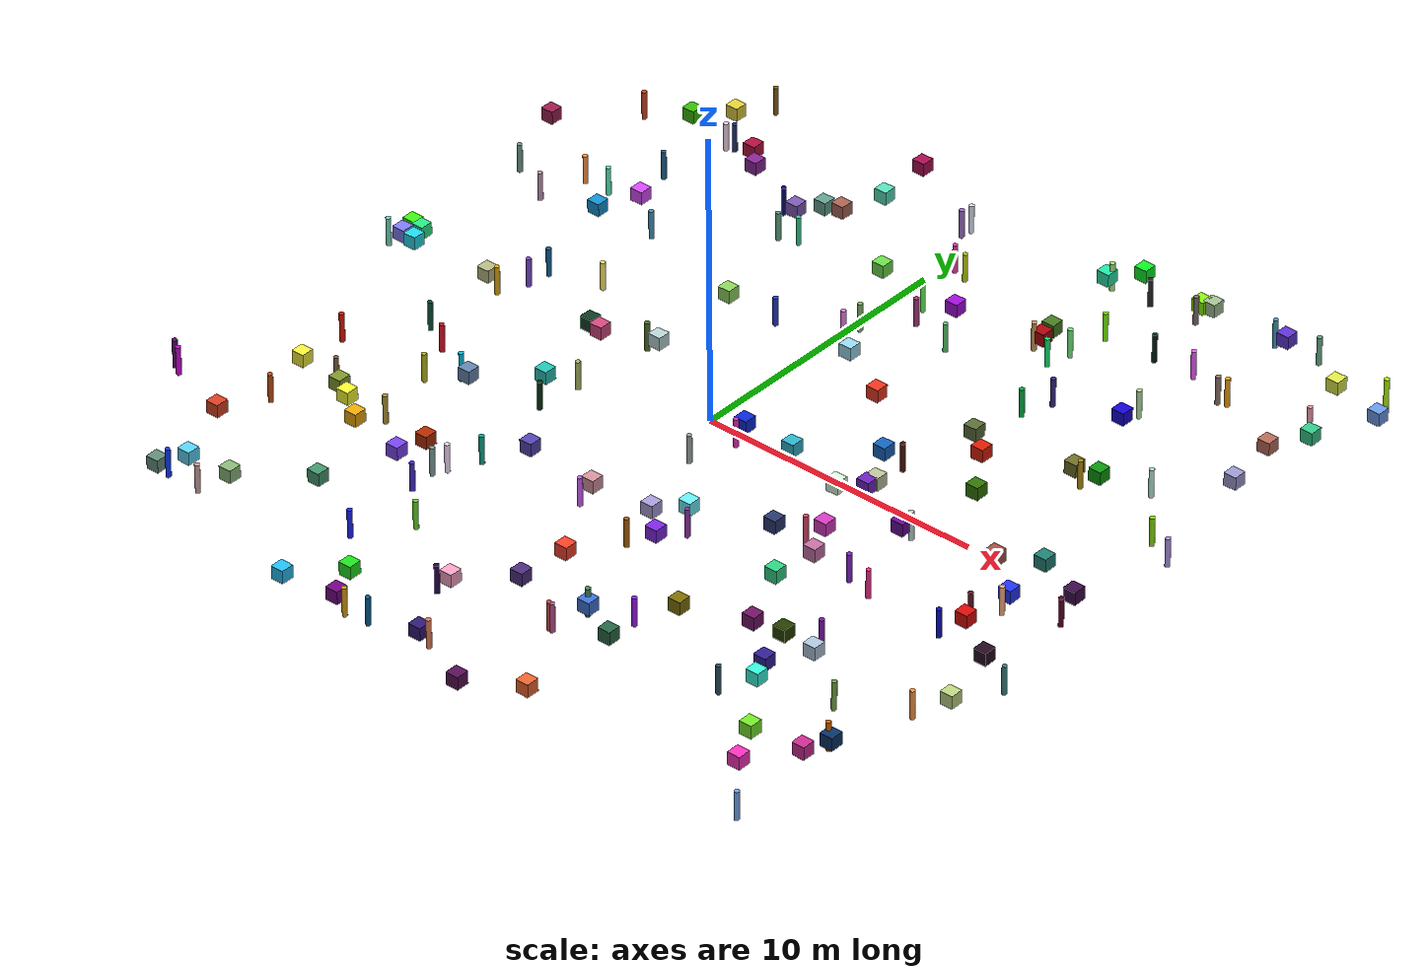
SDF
<sdf version="1.7">
 <world name="warehouse">
  <physics type="ode"><max_step_size>0.003</max_step_size><real_time_factor>1.0</real_time_factor></physics>
  <plugin name="ignition::gazebo::systems::Physics" filename="libignition-gazebo-physics-system.so"/>
  <plugin name="ignition::gazebo::systems::UserCommands" filename="libignition-gazebo-user-commands-system.so"/>
  <plugin name="ignition::gazebo::systems::SceneBroadcaster" filename="libignition-gazebo-scene-broadcaster-system.so"/>
  <plugin name="ignition::gazebo::systems::Sensors" filename="libignition-gazebo-sensors-system.so">
   <render_engine>ogre2</render_engine>
  </plugin>
  <plugin name="ignition::gazebo::systems::Imu" filename="libignition-gazebo-imu-system.so"/>
  <plugin name="ignition::gazebo::systems::NavSat" filename="libignition-gazebo-navsat-system.so"/>
  <scene>
   <ambient>1 1 1 1</ambient>
   <background>0 0 0 1</background>
   <shadows>0</shadows>
   <grid>false</grid>
  </scene>
  <spherical_coordinates>
   <surface_model>EARTH_WGS84</surface_model>
   <world_frame_orientation>ENU</world_frame_orientation>
   <latitude_deg>-22.986687</latitude_deg>
   <longitude_deg>-43.202501</longitude_deg>
   <elevation>0</elevation>
   <heading_deg>0</heading_deg>
  </spherical_coordinates>
  <model name="ground_plane">
   <static>true</static>
   <link name="link">
    <collision name="collision">
     <geometry><plane><normal>0.0 0.0 1</normal><size>1 1</size></plane></geometry>
    </collision>
   </link>
  </model>
  <model name="unit_box_0">
   <static>true</static>
   <pose>4.86 14.7 0 0 0 0</pose>
   <link name="link">
    <collision name="collision">
     <geometry><box><size>0.450000 0.450000 0.450000</size></box></geometry>
    </collision>
    <visual name="visual">
     <geometry><box><size>0.450000 0.450000 0.450000</size></box></geometry>
     <material>
      <ambient>0.0440894479829993 0.9466540511849011 0.1446051926658367 1</ambient>
      <diffuse>0.0440894479829993 0.9466540511849011 0.1446051926658367 1</diffuse>
      <script><uri>file://media/materials/scripts/gazebo.material</uri><name>Gazebo/RandomColor0</name></script>
     </material>
    </visual>
   </link>
  </model>
  <model name="unit_cylinder_0">
   <static>true</static>
   <pose>-12.4 6.25 0 0 0 0</pose>
   <link name="link">
    <collision name="collision">
     <geometry><cylinder><radius>0.085000</radius><length>1.000000</length></cylinder></geometry>
    </collision>
    <visual name="visual">
     <geometry><cylinder><radius>0.085000</radius><length>1.000000</length></cylinder></geometry>
     <material>
      <ambient>0.7270386856249603 0.569772761326217 0.6874630231590428 1</ambient>
      <diffuse>0.7270386856249603 0.569772761326217 0.6874630231590428 1</diffuse>
      <script><uri>file://media/materials/scripts/gazebo.material</uri><name>Gazebo/RandomColor0</name></script>
     </material>
    </visual>
   </link>
  </model>
  <model name="unit_box_1">
   <static>true</static>
   <pose>4.12 13.78 0 0 0 0</pose>
   <link name="link">
    <collision name="collision">
     <geometry><box><size>0.450000 0.450000 0.450000</size></box></geometry>
    </collision>
    <visual name="visual">
     <geometry><box><size>0.450000 0.450000 0.450000</size></box></geometry>
     <material>
      <ambient>0.13936809683720985 0.9011202749563527 0.6622935414420614 1</ambient>
      <diffuse>0.13936809683720985 0.9011202749563527 0.6622935414420614 1</diffuse>
      <script><uri>file://media/materials/scripts/gazebo.material</uri><name>Gazebo/RandomColor1</name></script>
     </material>
    </visual>
   </link>
  </model>
  <model name="unit_cylinder_1">
   <static>true</static>
   <pose>7.35 14.08 0 0 0 0</pose>
   <link name="link">
    <collision name="collision">
     <geometry><cylinder><radius>0.085000</radius><length>1.000000</length></cylinder></geometry>
    </collision>
    <visual name="visual">
     <geometry><cylinder><radius>0.085000</radius><length>1.000000</length></cylinder></geometry>
     <material>
      <ambient>0.4892112773507925 0.4217328960785478 0.3929808659382936 1</ambient>
      <diffuse>0.4892112773507925 0.4217328960785478 0.3929808659382936 1</diffuse>
      <script><uri>file://media/materials/scripts/gazebo.material</uri><name>Gazebo/RandomColor1</name></script>
     </material>
    </visual>
   </link>
  </model>
  <model name="unit_box_2">
   <static>true</static>
   <pose>5.68 0.53 0 0 0 0</pose>
   <link name="link">
    <collision name="collision">
     <geometry><box><size>0.450000 0.450000 0.450000</size></box></geometry>
    </collision>
    <visual name="visual">
     <geometry><box><size>0.450000 0.450000 0.450000</size></box></geometry>
     <material>
      <ambient>0.4295884488853311 0.1320019734991711 0.7548802276800174 1</ambient>
      <diffuse>0.4295884488853311 0.1320019734991711 0.7548802276800174 1</diffuse>
      <script><uri>file://media/materials/scripts/gazebo.material</uri><name>Gazebo/RandomColor2</name></script>
     </material>
    </visual>
   </link>
  </model>
  <model name="unit_cylinder_2">
   <static>true</static>
   <pose>-4.9 -6.97 0 0 0 0</pose>
   <link name="link">
    <collision name="collision">
     <geometry><cylinder><radius>0.085000</radius><length>1.000000</length></cylinder></geometry>
    </collision>
    <visual name="visual">
     <geometry><cylinder><radius>0.085000</radius><length>1.000000</length></cylinder></geometry>
     <material>
      <ambient>0.48882169617900995 0.6281090008410105 0.6111962959191779 1</ambient>
      <diffuse>0.48882169617900995 0.6281090008410105 0.6111962959191779 1</diffuse>
      <script><uri>file://media/materials/scripts/gazebo.material</uri><name>Gazebo/RandomColor2</name></script>
     </material>
    </visual>
   </link>
  </model>
  <model name="unit_box_3">
   <static>true</static>
   <pose>10.89 -10.85 0 0 0 0</pose>
   <link name="link">
    <collision name="collision">
     <geometry><box><size>0.450000 0.450000 0.450000</size></box></geometry>
    </collision>
    <visual name="visual">
     <geometry><box><size>0.450000 0.450000 0.450000</size></box></geometry>
     <material>
      <ambient>0.4624867590474331 0.9143126628185029 0.1579698359249163 1</ambient>
      <diffuse>0.4624867590474331 0.9143126628185029 0.1579698359249163 1</diffuse>
      <script><uri>file://media/materials/scripts/gazebo.material</uri><name>Gazebo/RandomColor3</name></script>
     </material>
    </visual>
   </link>
  </model>
  <model name="unit_cylinder_3">
   <static>true</static>
   <pose>14.11 -0.75 0 0 0 0</pose>
   <link name="link">
    <collision name="collision">
     <geometry><cylinder><radius>0.085000</radius><length>1.000000</length></cylinder></geometry>
    </collision>
    <visual name="visual">
     <geometry><cylinder><radius>0.085000</radius><length>1.000000</length></cylinder></geometry>
     <material>
      <ambient>0.31413875885268494 0.01794644405934065 0.1373584163908963 1</ambient>
      <diffuse>0.31413875885268494 0.01794644405934065 0.1373584163908963 1</diffuse>
      <script><uri>file://media/materials/scripts/gazebo.material</uri><name>Gazebo/RandomColor3</name></script>
     </material>
    </visual>
   </link>
  </model>
  <model name="unit_box_4">
   <static>true</static>
   <pose>-13.58 2.07 0 0 0 0</pose>
   <link name="link">
    <collision name="collision">
     <geometry><box><size>0.450000 0.450000 0.450000</size></box></geometry>
    </collision>
    <visual name="visual">
     <geometry><box><size>0.450000 0.450000 0.450000</size></box></geometry>
     <material>
      <ambient>0.15437058983870744 0.9188239497218856 0.5189726235144633 1</ambient>
      <diffuse>0.15437058983870744 0.9188239497218856 0.5189726235144633 1</diffuse>
      <script><uri>file://media/materials/scripts/gazebo.material</uri><name>Gazebo/RandomColor4</name></script>
     </material>
    </visual>
   </link>
  </model>
  <model name="unit_cylinder_4">
   <static>true</static>
   <pose>5.69 13.94 0 0 0 0</pose>
   <link name="link">
    <collision name="collision">
     <geometry><cylinder><radius>0.085000</radius><length>1.000000</length></cylinder></geometry>
    </collision>
    <visual name="visual">
     <geometry><cylinder><radius>0.085000</radius><length>1.000000</length></cylinder></geometry>
     <material>
      <ambient>0.1341796096800415 0.15039961002780222 0.16592342121938808 1</ambient>
      <diffuse>0.1341796096800415 0.15039961002780222 0.16592342121938808 1</diffuse>
      <script><uri>file://media/materials/scripts/gazebo.material</uri><name>Gazebo/RandomColor4</name></script>
     </material>
    </visual>
   </link>
  </model>
  <model name="unit_box_5">
   <static>true</static>
   <pose>-5.43 -1.33 0 0 0 0</pose>
   <link name="link">
    <collision name="collision">
     <geometry><box><size>0.450000 0.450000 0.450000</size></box></geometry>
    </collision>
    <visual name="visual">
     <geometry><box><size>0.450000 0.450000 0.450000</size></box></geometry>
     <material>
      <ambient>0.1437150085725608 0.771430351193349 0.7161037341647061 1</ambient>
      <diffuse>0.1437150085725608 0.771430351193349 0.7161037341647061 1</diffuse>
      <script><uri>file://media/materials/scripts/gazebo.material</uri><name>Gazebo/RandomColor5</name></script>
     </material>
    </visual>
   </link>
  </model>
  <model name="unit_cylinder_5">
   <static>true</static>
   <pose>13.59 4.13 0 0 0 0</pose>
   <link name="link">
    <collision name="collision">
     <geometry><cylinder><radius>0.085000</radius><length>1.000000</length></cylinder></geometry>
    </collision>
    <visual name="visual">
     <geometry><cylinder><radius>0.085000</radius><length>1.000000</length></cylinder></geometry>
     <material>
      <ambient>0.5082832375055166 0.8693185021433103 0.04404943998753352 1</ambient>
      <diffuse>0.5082832375055166 0.8693185021433103 0.04404943998753352 1</diffuse>
      <script><uri>file://media/materials/scripts/gazebo.material</uri><name>Gazebo/RandomColor5</name></script>
     </material>
    </visual>
   </link>
  </model>
  <model name="unit_box_6">
   <static>true</static>
   <pose>0.7 5.61 0 0 0 0</pose>
   <link name="link">
    <collision name="collision">
     <geometry><box><size>0.450000 0.450000 0.450000</size></box></geometry>
    </collision>
    <visual name="visual">
     <geometry><box><size>0.450000 0.450000 0.450000</size></box></geometry>
     <material>
      <ambient>0.6019330902248561 0.8545485791242867 0.9463620129433569 1</ambient>
      <diffuse>0.6019330902248561 0.8545485791242867 0.9463620129433569 1</diffuse>
      <script><uri>file://media/materials/scripts/gazebo.material</uri><name>Gazebo/RandomColor6</name></script>
     </material>
    </visual>
   </link>
  </model>
  <model name="unit_cylinder_6">
   <static>true</static>
   <pose>-11.76 -3.5 0 0 0 0</pose>
   <link name="link">
    <collision name="collision">
     <geometry><cylinder><radius>0.085000</radius><length>1.000000</length></cylinder></geometry>
    </collision>
    <visual name="visual">
     <geometry><cylinder><radius>0.085000</radius><length>1.000000</length></cylinder></geometry>
     <material>
      <ambient>0.8541178800004999 0.09001837165716808 0.022911375265942335 1</ambient>
      <diffuse>0.8541178800004999 0.09001837165716808 0.022911375265942335 1</diffuse>
      <script><uri>file://media/materials/scripts/gazebo.material</uri><name>Gazebo/RandomColor6</name></script>
     </material>
    </visual>
   </link>
  </model>
  <model name="unit_box_7">
   <static>true</static>
   <pose>-5.76 1.54 0 0 0 0</pose>
   <link name="link">
    <collision name="collision">
     <geometry><box><size>0.450000 0.450000 0.450000</size></box></geometry>
    </collision>
    <visual name="visual">
     <geometry><box><size>0.450000 0.450000 0.450000</size></box></geometry>
     <material>
      <ambient>0.8244783112689469 0.27947235165206885 0.4979456995320882 1</ambient>
      <diffuse>0.8244783112689469 0.27947235165206885 0.4979456995320882 1</diffuse>
      <script><uri>file://media/materials/scripts/gazebo.material</uri><name>Gazebo/RandomColor7</name></script>
     </material>
    </visual>
   </link>
  </model>
  <model name="unit_cylinder_7">
   <static>true</static>
   <pose>5.82 11.59 0 0 0 0</pose>
   <link name="link">
    <collision name="collision">
     <geometry><cylinder><radius>0.085000</radius><length>1.000000</length></cylinder></geometry>
    </collision>
    <visual name="visual">
     <geometry><cylinder><radius>0.085000</radius><length>1.000000</length></cylinder></geometry>
     <material>
      <ambient>0.4614413156698295 0.9580878596213448 0.015944803376221728 1</ambient>
      <diffuse>0.4614413156698295 0.9580878596213448 0.015944803376221728 1</diffuse>
      <script><uri>file://media/materials/scripts/gazebo.material</uri><name>Gazebo/RandomColor7</name></script>
     </material>
    </visual>
   </link>
  </model>
  <model name="unit_box_8">
   <static>true</static>
   <pose>4.89 2.23 0 0 0 0</pose>
   <link name="link">
    <collision name="collision">
     <geometry><box><size>0.450000 0.450000 0.450000</size></box></geometry>
    </collision>
    <visual name="visual">
     <geometry><box><size>0.450000 0.450000 0.450000</size></box></geometry>
     <material>
      <ambient>0.0728688957714253 0.39289916852559303 0.7492032021296913 1</ambient>
      <diffuse>0.0728688957714253 0.39289916852559303 0.7492032021296913 1</diffuse>
      <script><uri>file://media/materials/scripts/gazebo.material</uri><name>Gazebo/RandomColor8</name></script>
     </material>
    </visual>
   </link>
  </model>
  <model name="unit_cylinder_8">
   <static>true</static>
   <pose>12.03 6.05 0 0 0 0</pose>
   <link name="link">
    <collision name="collision">
     <geometry><cylinder><radius>0.085000</radius><length>1.000000</length></cylinder></geometry>
    </collision>
    <visual name="visual">
     <geometry><cylinder><radius>0.085000</radius><length>1.000000</length></cylinder></geometry>
     <material>
      <ambient>0.7076495968020946 0.9175697631631726 0.8125382040000438 1</ambient>
      <diffuse>0.7076495968020946 0.9175697631631726 0.8125382040000438 1</diffuse>
      <script><uri>file://media/materials/scripts/gazebo.material</uri><name>Gazebo/RandomColor8</name></script>
     </material>
    </visual>
   </link>
  </model>
  <model name="unit_box_9">
   <static>true</static>
   <pose>8.6 -6.69 0 0 0 0</pose>
   <link name="link">
    <collision name="collision">
     <geometry><box><size>0.450000 0.450000 0.450000</size></box></geometry>
    </collision>
    <visual name="visual">
     <geometry><box><size>0.450000 0.450000 0.450000</size></box></geometry>
     <material>
      <ambient>0.14614154093612663 0.23697075493477127 0.0011599974244516087 1</ambient>
      <diffuse>0.14614154093612663 0.23697075493477127 0.0011599974244516087 1</diffuse>
      <script><uri>file://media/materials/scripts/gazebo.material</uri><name>Gazebo/RandomColor9</name></script>
     </material>
    </visual>
   </link>
  </model>
  <model name="unit_cylinder_9">
   <static>true</static>
   <pose>-4.68 -6.55 0 0 0 0</pose>
   <link name="link">
    <collision name="collision">
     <geometry><cylinder><radius>0.085000</radius><length>1.000000</length></cylinder></geometry>
    </collision>
    <visual name="visual">
     <geometry><cylinder><radius>0.085000</radius><length>1.000000</length></cylinder></geometry>
     <material>
      <ambient>0.9647823803268121 0.8732027528752004 0.9992866168511414 1</ambient>
      <diffuse>0.9647823803268121 0.8732027528752004 0.9992866168511414 1</diffuse>
      <script><uri>file://media/materials/scripts/gazebo.material</uri><name>Gazebo/RandomColor9</name></script>
     </material>
    </visual>
   </link>
  </model>
  <model name="unit_box_10">
   <static>true</static>
   <pose>4.6 10.53 0 0 0 0</pose>
   <link name="link">
    <collision name="collision">
     <geometry><box><size>0.450000 0.450000 0.450000</size></box></geometry>
    </collision>
    <visual name="visual">
     <geometry><box><size>0.450000 0.450000 0.450000</size></box></geometry>
     <material>
      <ambient>0.268791510697008 0.48887328501884375 0.13953731876235898 1</ambient>
      <diffuse>0.268791510697008 0.48887328501884375 0.13953731876235898 1</diffuse>
      <script><uri>file://media/materials/scripts/gazebo.material</uri><name>Gazebo/RandomColor10</name></script>
     </material>
    </visual>
   </link>
  </model>
  <model name="unit_cylinder_10">
   <static>true</static>
   <pose>-10.3 -5.33 0 0 0 0</pose>
   <link name="link">
    <collision name="collision">
     <geometry><cylinder><radius>0.085000</radius><length>1.000000</length></cylinder></geometry>
    </collision>
    <visual name="visual">
     <geometry><cylinder><radius>0.085000</radius><length>1.000000</length></cylinder></geometry>
     <material>
      <ambient>0.4950050222993094 0.36748113770023316 0.22922007542965583 1</ambient>
      <diffuse>0.4950050222993094 0.36748113770023316 0.22922007542965583 1</diffuse>
      <script><uri>file://media/materials/scripts/gazebo.material</uri><name>Gazebo/RandomColor10</name></script>
     </material>
    </visual>
   </link>
  </model>
  <model name="unit_box_11">
   <static>true</static>
   <pose>4.73 -13.51 0 0 0 0</pose>
   <link name="link">
    <collision name="collision">
     <geometry><box><size>0.450000 0.450000 0.450000</size></box></geometry>
    </collision>
    <visual name="visual">
     <geometry><box><size>0.450000 0.450000 0.450000</size></box></geometry>
     <material>
      <ambient>0.9340203933268564 0.39520919700550494 0.18268924808897258 1</ambient>
      <diffuse>0.9340203933268564 0.39520919700550494 0.18268924808897258 1</diffuse>
      <script><uri>file://media/materials/scripts/gazebo.material</uri><name>Gazebo/RandomColor11</name></script>
     </material>
    </visual>
   </link>
  </model>
  <model name="unit_cylinder_11">
   <static>true</static>
   <pose>-10.81 -12.13 0 0 0 0</pose>
   <link name="link">
    <collision name="collision">
     <geometry><cylinder><radius>0.085000</radius><length>1.000000</length></cylinder></geometry>
    </collision>
    <visual name="visual">
     <geometry><cylinder><radius>0.085000</radius><length>1.000000</length></cylinder></geometry>
     <material>
      <ambient>0.04214225447750308 0.2186785520565364 0.993793384665782 1</ambient>
      <diffuse>0.04214225447750308 0.2186785520565364 0.993793384665782 1</diffuse>
      <script><uri>file://media/materials/scripts/gazebo.material</uri><name>Gazebo/RandomColor11</name></script>
     </material>
    </visual>
   </link>
  </model>
  <model name="unit_box_12">
   <static>true</static>
   <pose>10.86 0.2 0 0 0 0</pose>
   <link name="link">
    <collision name="collision">
     <geometry><box><size>0.450000 0.450000 0.450000</size></box></geometry>
    </collision>
    <visual name="visual">
     <geometry><box><size>0.450000 0.450000 0.450000</size></box></geometry>
     <material>
      <ambient>0.6375677313072791 0.31348500282331193 0.27738088615342893 1</ambient>
      <diffuse>0.6375677313072791 0.31348500282331193 0.27738088615342893 1</diffuse>
      <script><uri>file://media/materials/scripts/gazebo.material</uri><name>Gazebo/RandomColor12</name></script>
     </material>
    </visual>
   </link>
  </model>
  <model name="unit_cylinder_12">
   <static>true</static>
   <pose>-9.37 3.25 0 0 0 0</pose>
   <link name="link">
    <collision name="collision">
     <geometry><cylinder><radius>0.085000</radius><length>1.000000</length></cylinder></geometry>
    </collision>
    <visual name="visual">
     <geometry><cylinder><radius>0.085000</radius><length>1.000000</length></cylinder></geometry>
     <material>
      <ambient>0.06544878131439513 0.3690667785904276 0.5863571859016304 1</ambient>
      <diffuse>0.06544878131439513 0.3690667785904276 0.5863571859016304 1</diffuse>
      <script><uri>file://media/materials/scripts/gazebo.material</uri><name>Gazebo/RandomColor12</name></script>
     </material>
    </visual>
   </link>
  </model>
  <model name="unit_box_13">
   <static>true</static>
   <pose>-7.0 -9.69 0 0 0 0</pose>
   <link name="link">
    <collision name="collision">
     <geometry><box><size>0.450000 0.450000 0.450000</size></box></geometry>
    </collision>
    <visual name="visual">
     <geometry><box><size>0.450000 0.450000 0.450000</size></box></geometry>
     <material>
      <ambient>0.26723961633187265 0.594587258055126 0.43162423170698283 1</ambient>
      <diffuse>0.26723961633187265 0.594587258055126 0.43162423170698283 1</diffuse>
      <script><uri>file://media/materials/scripts/gazebo.material</uri><name>Gazebo/RandomColor13</name></script>
     </material>
    </visual>
   </link>
  </model>
  <model name="unit_cylinder_13">
   <static>true</static>
   <pose>-11.97 7.88 0 0 0 0</pose>
   <link name="link">
    <collision name="collision">
     <geometry><cylinder><radius>0.085000</radius><length>1.000000</length></cylinder></geometry>
    </collision>
    <visual name="visual">
     <geometry><cylinder><radius>0.085000</radius><length>1.000000</length></cylinder></geometry>
     <material>
      <ambient>0.995783059129133 0.5780543401211613 0.259541788408418 1</ambient>
      <diffuse>0.995783059129133 0.5780543401211613 0.259541788408418 1</diffuse>
      <script><uri>file://media/materials/scripts/gazebo.material</uri><name>Gazebo/RandomColor13</name></script>
     </material>
    </visual>
   </link>
  </model>
  <model name="unit_box_14">
   <static>true</static>
   <pose>10.38 14.68 0 0 0 0</pose>
   <link name="link">
    <collision name="collision">
     <geometry><box><size>0.450000 0.450000 0.450000</size></box></geometry>
    </collision>
    <visual name="visual">
     <geometry><box><size>0.450000 0.450000 0.450000</size></box></geometry>
     <material>
      <ambient>0.3736737728089504 0.19853963764873406 0.8304825299455667 1</ambient>
      <diffuse>0.3736737728089504 0.19853963764873406 0.8304825299455667 1</diffuse>
      <script><uri>file://media/materials/scripts/gazebo.material</uri><name>Gazebo/RandomColor14</name></script>
     </material>
    </visual>
   </link>
  </model>
  <model name="unit_cylinder_14">
   <static>true</static>
   <pose>-0.31 6.53 0 0 0 0</pose>
   <link name="link">
    <collision name="collision">
     <geometry><cylinder><radius>0.085000</radius><length>1.000000</length></cylinder></geometry>
    </collision>
    <visual name="visual">
     <geometry><cylinder><radius>0.085000</radius><length>1.000000</length></cylinder></geometry>
     <material>
      <ambient>0.9418872741472382 0.4807056358799212 0.9225043756003432 1</ambient>
      <diffuse>0.9418872741472382 0.4807056358799212 0.9225043756003432 1</diffuse>
      <script><uri>file://media/materials/scripts/gazebo.material</uri><name>Gazebo/RandomColor14</name></script>
     </material>
    </visual>
   </link>
  </model>
  <model name="unit_box_15">
   <static>true</static>
   <pose>13.41 9.87 0 0 0 0</pose>
   <link name="link">
    <collision name="collision">
     <geometry><box><size>0.450000 0.450000 0.450000</size></box></geometry>
    </collision>
    <visual name="visual">
     <geometry><box><size>0.450000 0.450000 0.450000</size></box></geometry>
     <material>
      <ambient>0.7269252845706303 0.4199841115753088 0.3438289820375734 1</ambient>
      <diffuse>0.7269252845706303 0.4199841115753088 0.3438289820375734 1</diffuse>
      <script><uri>file://media/materials/scripts/gazebo.material</uri><name>Gazebo/RandomColor15</name></script>
     </material>
    </visual>
   </link>
  </model>
  <model name="unit_cylinder_15">
   <static>true</static>
   <pose>0.52 11.32 0 0 0 0</pose>
   <link name="link">
    <collision name="collision">
     <geometry><cylinder><radius>0.085000</radius><length>1.000000</length></cylinder></geometry>
    </collision>
    <visual name="visual">
     <geometry><cylinder><radius>0.085000</radius><length>1.000000</length></cylinder></geometry>
     <material>
      <ambient>0.7412902797736225 0.8152631183749225 0.0652345516483388 1</ambient>
      <diffuse>0.7412902797736225 0.8152631183749225 0.0652345516483388 1</diffuse>
      <script><uri>file://media/materials/scripts/gazebo.material</uri><name>Gazebo/RandomColor15</name></script>
     </material>
    </visual>
   </link>
  </model>
  <model name="unit_box_16">
   <static>true</static>
   <pose>7.62 14.58 0 0 0 0</pose>
   <link name="link">
    <collision name="collision">
     <geometry><box><size>0.450000 0.450000 0.450000</size></box></geometry>
    </collision>
    <visual name="visual">
     <geometry><box><size>0.450000 0.450000 0.450000</size></box></geometry>
     <material>
      <ambient>0.6364192580588337 0.7606513629192436 0.5742180573632772 1</ambient>
      <diffuse>0.6364192580588337 0.7606513629192436 0.5742180573632772 1</diffuse>
      <script><uri>file://media/materials/scripts/gazebo.material</uri><name>Gazebo/RandomColor16</name></script>
     </material>
    </visual>
   </link>
  </model>
  <model name="unit_cylinder_16">
   <static>true</static>
   <pose>0.6 9.2 0 0 0 0</pose>
   <link name="link">
    <collision name="collision">
     <geometry><cylinder><radius>0.085000</radius><length>1.000000</length></cylinder></geometry>
    </collision>
    <visual name="visual">
     <geometry><cylinder><radius>0.085000</radius><length>1.000000</length></cylinder></geometry>
     <material>
      <ambient>0.3779723460318357 0.9465149101639637 0.336937077792953 1</ambient>
      <diffuse>0.3779723460318357 0.9465149101639637 0.336937077792953 1</diffuse>
      <script><uri>file://media/materials/scripts/gazebo.material</uri><name>Gazebo/RandomColor16</name></script>
     </material>
    </visual>
   </link>
  </model>
  <model name="unit_box_17">
   <static>true</static>
   <pose>-13.9 1.58 0 0 0 0</pose>
   <link name="link">
    <collision name="collision">
     <geometry><box><size>0.450000 0.450000 0.450000</size></box></geometry>
    </collision>
    <visual name="visual">
     <geometry><box><size>0.450000 0.450000 0.450000</size></box></geometry>
     <material>
      <ambient>0.4912069242863344 0.4825291535516151 0.9687258591366672 1</ambient>
      <diffuse>0.4912069242863344 0.4825291535516151 0.9687258591366672 1</diffuse>
      <script><uri>file://media/materials/scripts/gazebo.material</uri><name>Gazebo/RandomColor17</name></script>
     </material>
    </visual>
   </link>
  </model>
  <model name="unit_cylinder_17">
   <static>true</static>
   <pose>14.59 3.61 0 0 0 0</pose>
   <link name="link">
    <collision name="collision">
     <geometry><cylinder><radius>0.085000</radius><length>1.000000</length></cylinder></geometry>
    </collision>
    <visual name="visual">
     <geometry><cylinder><radius>0.085000</radius><length>1.000000</length></cylinder></geometry>
     <material>
      <ambient>0.6854748888082745 0.5704663235262069 0.9003668782187838 1</ambient>
      <diffuse>0.6854748888082745 0.5704663235262069 0.9003668782187838 1</diffuse>
      <script><uri>file://media/materials/scripts/gazebo.material</uri><name>Gazebo/RandomColor17</name></script>
     </material>
    </visual>
   </link>
  </model>
  <model name="unit_box_18">
   <static>true</static>
   <pose>4.83 -10.08 0 0 0 0</pose>
   <link name="link">
    <collision name="collision">
     <geometry><box><size>0.450000 0.450000 0.450000</size></box></geometry>
    </collision>
    <visual name="visual">
     <geometry><box><size>0.450000 0.450000 0.450000</size></box></geometry>
     <material>
      <ambient>0.15213708138282123 0.401753758546899 0.2688642279360097 1</ambient>
      <diffuse>0.15213708138282123 0.401753758546899 0.2688642279360097 1</diffuse>
      <script><uri>file://media/materials/scripts/gazebo.material</uri><name>Gazebo/RandomColor18</name></script>
     </material>
    </visual>
   </link>
  </model>
  <model name="unit_cylinder_18">
   <static>true</static>
   <pose>0.88 -13.47 0 0 0 0</pose>
   <link name="link">
    <collision name="collision">
     <geometry><cylinder><radius>0.085000</radius><length>1.000000</length></cylinder></geometry>
    </collision>
    <visual name="visual">
     <geometry><cylinder><radius>0.085000</radius><length>1.000000</length></cylinder></geometry>
     <material>
      <ambient>0.889661844785997 0.4847488373577973 0.3384738342592306 1</ambient>
      <diffuse>0.889661844785997 0.4847488373577973 0.3384738342592306 1</diffuse>
      <script><uri>file://media/materials/scripts/gazebo.material</uri><name>Gazebo/RandomColor18</name></script>
     </material>
    </visual>
   </link>
  </model>
  <model name="unit_box_19">
   <static>true</static>
   <pose>-0.58 -4.69 0 0 0 0</pose>
   <link name="link">
    <collision name="collision">
     <geometry><box><size>0.450000 0.450000 0.450000</size></box></geometry>
    </collision>
    <visual name="visual">
     <geometry><box><size>0.450000 0.450000 0.450000</size></box></geometry>
     <material>
      <ambient>0.8342006538471091 0.5773219657345021 0.6333201078097498 1</ambient>
      <diffuse>0.8342006538471091 0.5773219657345021 0.6333201078097498 1</diffuse>
      <script><uri>file://media/materials/scripts/gazebo.material</uri><name>Gazebo/RandomColor19</name></script>
     </material>
    </visual>
   </link>
  </model>
  <model name="unit_cylinder_19">
   <static>true</static>
   <pose>8.95 -3.3 0 0 0 0</pose>
   <link name="link">
    <collision name="collision">
     <geometry><cylinder><radius>0.085000</radius><length>1.000000</length></cylinder></geometry>
    </collision>
    <visual name="visual">
     <geometry><cylinder><radius>0.085000</radius><length>1.000000</length></cylinder></geometry>
     <material>
      <ambient>0.9456553254621518 0.16936506476351731 0.5296005652481653 1</ambient>
      <diffuse>0.9456553254621518 0.16936506476351731 0.5296005652481653 1</diffuse>
      <script><uri>file://media/materials/scripts/gazebo.material</uri><name>Gazebo/RandomColor19</name></script>
     </material>
    </visual>
   </link>
  </model>
  <model name="unit_box_20">
   <static>true</static>
   <pose>-4.14 14.88 0 0 0 0</pose>
   <link name="link">
    <collision name="collision">
     <geometry><box><size>0.450000 0.450000 0.450000</size></box></geometry>
    </collision>
    <visual name="visual">
     <geometry><box><size>0.450000 0.450000 0.450000</size></box></geometry>
     <material>
      <ambient>0.6570899015671107 0.04959333228282392 0.3146562197480839 1</ambient>
      <diffuse>0.6570899015671107 0.04959333228282392 0.3146562197480839 1</diffuse>
      <script><uri>file://media/materials/scripts/gazebo.material</uri><name>Gazebo/RandomColor20</name></script>
     </material>
    </visual>
   </link>
  </model>
  <model name="unit_cylinder_20">
   <static>true</static>
   <pose>-8.36 6.87 0 0 0 0</pose>
   <link name="link">
    <collision name="collision">
     <geometry><cylinder><radius>0.085000</radius><length>1.000000</length></cylinder></geometry>
    </collision>
    <visual name="visual">
     <geometry><cylinder><radius>0.085000</radius><length>1.000000</length></cylinder></geometry>
     <material>
      <ambient>0.24812325368981236 0.5832464418912141 0.7202497818833877 1</ambient>
      <diffuse>0.24812325368981236 0.5832464418912141 0.7202497818833877 1</diffuse>
      <script><uri>file://media/materials/scripts/gazebo.material</uri><name>Gazebo/RandomColor20</name></script>
     </material>
    </visual>
   </link>
  </model>
  <model name="unit_box_21">
   <static>true</static>
   <pose>7.79 -0.42 0 0 0 0</pose>
   <link name="link">
    <collision name="collision">
     <geometry><box><size>0.450000 0.450000 0.450000</size></box></geometry>
    </collision>
    <visual name="visual">
     <geometry><box><size>0.450000 0.450000 0.450000</size></box></geometry>
     <material>
      <ambient>0.38801801391914703 0.03405274313850837 0.5868825694169122 1</ambient>
      <diffuse>0.38801801391914703 0.03405274313850837 0.5868825694169122 1</diffuse>
      <script><uri>file://media/materials/scripts/gazebo.material</uri><name>Gazebo/RandomColor21</name></script>
     </material>
    </visual>
   </link>
  </model>
  <model name="unit_cylinder_21">
   <static>true</static>
   <pose>-9.62 12.27 0 0 0 0</pose>
   <link name="link">
    <collision name="collision">
     <geometry><cylinder><radius>0.085000</radius><length>1.000000</length></cylinder></geometry>
    </collision>
    <visual name="visual">
     <geometry><cylinder><radius>0.085000</radius><length>1.000000</length></cylinder></geometry>
     <material>
      <ambient>0.12439521310844526 0.16274525032053977 0.3672444559694883 1</ambient>
      <diffuse>0.12439521310844526 0.16274525032053977 0.3672444559694883 1</diffuse>
      <script><uri>file://media/materials/scripts/gazebo.material</uri><name>Gazebo/RandomColor21</name></script>
     </material>
    </visual>
   </link>
  </model>
  <model name="unit_box_22">
   <static>true</static>
   <pose>-9.22 -6.02 0 0 0 0</pose>
   <link name="link">
    <collision name="collision">
     <geometry><box><size>0.450000 0.450000 0.450000</size></box></geometry>
    </collision>
    <visual name="visual">
     <geometry><box><size>0.450000 0.450000 0.450000</size></box></geometry>
     <material>
      <ambient>0.9790693472931132 0.9973885884917622 0.19216060299283866 1</ambient>
      <diffuse>0.9790693472931132 0.9973885884917622 0.19216060299283866 1</diffuse>
      <script><uri>file://media/materials/scripts/gazebo.material</uri><name>Gazebo/RandomColor22</name></script>
     </material>
    </visual>
   </link>
  </model>
  <model name="unit_cylinder_22">
   <static>true</static>
   <pose>-7.61 3.76 0 0 0 0</pose>
   <link name="link">
    <collision name="collision">
     <geometry><cylinder><radius>0.085000</radius><length>1.000000</length></cylinder></geometry>
    </collision>
    <visual name="visual">
     <geometry><cylinder><radius>0.085000</radius><length>1.000000</length></cylinder></geometry>
     <material>
      <ambient>0.9892548789471347 0.917239920365452 0.40197223868547693 1</ambient>
      <diffuse>0.9892548789471347 0.917239920365452 0.40197223868547693 1</diffuse>
      <script><uri>file://media/materials/scripts/gazebo.material</uri><name>Gazebo/RandomColor22</name></script>
     </material>
    </visual>
   </link>
  </model>
  <model name="unit_box_23">
   <static>true</static>
   <pose>-3.25 -4.45 0 0 0 0</pose>
   <link name="link">
    <collision name="collision">
     <geometry><box><size>0.450000 0.450000 0.450000</size></box></geometry>
    </collision>
    <visual name="visual">
     <geometry><box><size>0.450000 0.450000 0.450000</size></box></geometry>
     <material>
      <ambient>0.326988515492164 0.266446417908078 0.6975832602943213 1</ambient>
      <diffuse>0.326988515492164 0.266446417908078 0.6975832602943213 1</diffuse>
      <script><uri>file://media/materials/scripts/gazebo.material</uri><name>Gazebo/RandomColor23</name></script>
     </material>
    </visual>
   </link>
  </model>
  <model name="unit_cylinder_23">
   <static>true</static>
   <pose>-10.99 7.85 0 0 0 0</pose>
   <link name="link">
    <collision name="collision">
     <geometry><cylinder><radius>0.085000</radius><length>1.000000</length></cylinder></geometry>
    </collision>
    <visual name="visual">
     <geometry><cylinder><radius>0.085000</radius><length>1.000000</length></cylinder></geometry>
     <material>
      <ambient>0.3342248740142649 0.9366365608871166 0.7146100990959178 1</ambient>
      <diffuse>0.3342248740142649 0.9366365608871166 0.7146100990959178 1</diffuse>
      <script><uri>file://media/materials/scripts/gazebo.material</uri><name>Gazebo/RandomColor23</name></script>
     </material>
    </visual>
   </link>
  </model>
  <model name="unit_box_24">
   <static>true</static>
   <pose>10.55 5.42 0 0 0 0</pose>
   <link name="link">
    <collision name="collision">
     <geometry><box><size>0.450000 0.450000 0.450000</size></box></geometry>
    </collision>
    <visual name="visual">
     <geometry><box><size>0.450000 0.450000 0.450000</size></box></geometry>
     <material>
      <ambient>0.03565029373189332 0.5989503622130179 0.0420726247608354 1</ambient>
      <diffuse>0.03565029373189332 0.5989503622130179 0.0420726247608354 1</diffuse>
      <script><uri>file://media/materials/scripts/gazebo.material</uri><name>Gazebo/RandomColor24</name></script>
     </material>
    </visual>
   </link>
  </model>
  <model name="unit_cylinder_24">
   <static>true</static>
   <pose>-2.04 -13.9 0 0 0 0</pose>
   <link name="link">
    <collision name="collision">
     <geometry><cylinder><radius>0.085000</radius><length>1.000000</length></cylinder></geometry>
    </collision>
    <visual name="visual">
     <geometry><cylinder><radius>0.085000</radius><length>1.000000</length></cylinder></geometry>
     <material>
      <ambient>0.8292453268627052 0.6054682728197773 0.07312862907861306 1</ambient>
      <diffuse>0.8292453268627052 0.6054682728197773 0.07312862907861306 1</diffuse>
      <script><uri>file://media/materials/scripts/gazebo.material</uri><name>Gazebo/RandomColor24</name></script>
     </material>
    </visual>
   </link>
  </model>
  <model name="unit_box_25">
   <static>true</static>
   <pose>12.15 -2.73 0 0 0 0</pose>
   <link name="link">
    <collision name="collision">
     <geometry><box><size>0.450000 0.450000 0.450000</size></box></geometry>
    </collision>
    <visual name="visual">
     <geometry><box><size>0.450000 0.450000 0.450000</size></box></geometry>
     <material>
      <ambient>0.8692494964949719 0.03779436172145079 0.03194965988478493 1</ambient>
      <diffuse>0.8692494964949719 0.03779436172145079 0.03194965988478493 1</diffuse>
      <script><uri>file://media/materials/scripts/gazebo.material</uri><name>Gazebo/RandomColor25</name></script>
     </material>
    </visual>
   </link>
  </model>
  <model name="unit_cylinder_25">
   <static>true</static>
   <pose>0.48 -1.52 0 0 0 0</pose>
   <link name="link">
    <collision name="collision">
     <geometry><cylinder><radius>0.085000</radius><length>1.000000</length></cylinder></geometry>
    </collision>
    <visual name="visual">
     <geometry><cylinder><radius>0.085000</radius><length>1.000000</length></cylinder></geometry>
     <material>
      <ambient>0.6107865553815773 0.6437235294481034 0.6124658333225681 1</ambient>
      <diffuse>0.6107865553815773 0.6437235294481034 0.6124658333225681 1</diffuse>
      <script><uri>file://media/materials/scripts/gazebo.material</uri><name>Gazebo/RandomColor25</name></script>
     </material>
    </visual>
   </link>
  </model>
  <model name="unit_box_26">
   <static>true</static>
   <pose>-9.75 7.96 0 0 0 0</pose>
   <link name="link">
    <collision name="collision">
     <geometry><box><size>0.450000 0.450000 0.450000</size></box></geometry>
    </collision>
    <visual name="visual">
     <geometry><box><size>0.450000 0.450000 0.450000</size></box></geometry>
     <material>
      <ambient>0.8415530832419882 0.3011689718070558 0.9932040617403763 1</ambient>
      <diffuse>0.8415530832419882 0.3011689718070558 0.9932040617403763 1</diffuse>
      <script><uri>file://media/materials/scripts/gazebo.material</uri><name>Gazebo/RandomColor26</name></script>
     </material>
    </visual>
   </link>
  </model>
  <model name="unit_cylinder_26">
   <static>true</static>
   <pose>14.97 -4.39 0 0 0 0</pose>
   <link name="link">
    <collision name="collision">
     <geometry><cylinder><radius>0.085000</radius><length>1.000000</length></cylinder></geometry>
    </collision>
    <visual name="visual">
     <geometry><cylinder><radius>0.085000</radius><length>1.000000</length></cylinder></geometry>
     <material>
      <ambient>0.21813894036833092 0.5031524766580354 0.49754303737141214 1</ambient>
      <diffuse>0.21813894036833092 0.5031524766580354 0.49754303737141214 1</diffuse>
      <script><uri>file://media/materials/scripts/gazebo.material</uri><name>Gazebo/RandomColor26</name></script>
     </material>
    </visual>
   </link>
  </model>
  <model name="unit_box_27">
   <static>true</static>
   <pose>4.96 -0.04 0 0 0 0</pose>
   <link name="link">
    <collision name="collision">
     <geometry><box><size>0.450000 0.450000 0.450000</size></box></geometry>
    </collision>
    <visual name="visual">
     <geometry><box><size>0.450000 0.450000 0.450000</size></box></geometry>
     <material>
      <ambient>0.8486869016865819 0.9941956500694433 0.852067054914752 1</ambient>
      <diffuse>0.8486869016865819 0.9941956500694433 0.852067054914752 1</diffuse>
      <script><uri>file://media/materials/scripts/gazebo.material</uri><name>Gazebo/RandomColor27</name></script>
     </material>
    </visual>
   </link>
  </model>
  <model name="unit_cylinder_27">
   <static>true</static>
   <pose>8.01 -3.06 0 0 0 0</pose>
   <link name="link">
    <collision name="collision">
     <geometry><cylinder><radius>0.085000</radius><length>1.000000</length></cylinder></geometry>
    </collision>
    <visual name="visual">
     <geometry><cylinder><radius>0.085000</radius><length>1.000000</length></cylinder></geometry>
     <material>
      <ambient>0.5099441863754836 0.1291536698231901 0.7783231246136362 1</ambient>
      <diffuse>0.5099441863754836 0.1291536698231901 0.7783231246136362 1</diffuse>
      <script><uri>file://media/materials/scripts/gazebo.material</uri><name>Gazebo/RandomColor27</name></script>
     </material>
    </visual>
   </link>
  </model>
  <model name="unit_box_28">
   <static>true</static>
   <pose>13.02 -9.8 0 0 0 0</pose>
   <link name="link">
    <collision name="collision">
     <geometry><box><size>0.450000 0.450000 0.450000</size></box></geometry>
    </collision>
    <visual name="visual">
     <geometry><box><size>0.450000 0.450000 0.450000</size></box></geometry>
     <material>
      <ambient>0.02478765518445203 0.19437383636729533 0.4042443228060443 1</ambient>
      <diffuse>0.02478765518445203 0.19437383636729533 0.4042443228060443 1</diffuse>
      <script><uri>file://media/materials/scripts/gazebo.material</uri><name>Gazebo/RandomColor28</name></script>
     </material>
    </visual>
   </link>
  </model>
  <model name="unit_cylinder_28">
   <static>true</static>
   <pose>13.6 11.66 0 0 0 0</pose>
   <link name="link">
    <collision name="collision">
     <geometry><cylinder><radius>0.085000</radius><length>1.000000</length></cylinder></geometry>
    </collision>
    <visual name="visual">
     <geometry><cylinder><radius>0.085000</radius><length>1.000000</length></cylinder></geometry>
     <material>
      <ambient>0.9450633978795633 0.6034795276451796 0.6650146412647179 1</ambient>
      <diffuse>0.9450633978795633 0.6034795276451796 0.6650146412647179 1</diffuse>
      <script><uri>file://media/materials/scripts/gazebo.material</uri><name>Gazebo/RandomColor28</name></script>
     </material>
    </visual>
   </link>
  </model>
  <model name="unit_box_29">
   <static>true</static>
   <pose>-10.62 13.49 0 0 0 0</pose>
   <link name="link">
    <collision name="collision">
     <geometry><box><size>0.450000 0.450000 0.450000</size></box></geometry>
    </collision>
    <visual name="visual">
     <geometry><box><size>0.450000 0.450000 0.450000</size></box></geometry>
     <material>
      <ambient>0.8966413880098881 0.8153487945042813 0.2292422976076619 1</ambient>
      <diffuse>0.8966413880098881 0.8153487945042813 0.2292422976076619 1</diffuse>
      <script><uri>file://media/materials/scripts/gazebo.material</uri><name>Gazebo/RandomColor29</name></script>
     </material>
    </visual>
   </link>
  </model>
  <model name="unit_cylinder_29">
   <static>true</static>
   <pose>-7.81 -5.86 0 0 0 0</pose>
   <link name="link">
    <collision name="collision">
     <geometry><cylinder><radius>0.085000</radius><length>1.000000</length></cylinder></geometry>
    </collision>
    <visual name="visual">
     <geometry><cylinder><radius>0.085000</radius><length>1.000000</length></cylinder></geometry>
     <material>
      <ambient>0.6778833269621279 0.5771833709296245 0.19220893541006578 1</ambient>
      <diffuse>0.6778833269621279 0.5771833709296245 0.19220893541006578 1</diffuse>
      <script><uri>file://media/materials/scripts/gazebo.material</uri><name>Gazebo/RandomColor29</name></script>
     </material>
    </visual>
   </link>
  </model>
  <model name="unit_box_30">
   <static>true</static>
   <pose>12.12 0.94 0 0 0 0</pose>
   <link name="link">
    <collision name="collision">
     <geometry><box><size>0.450000 0.450000 0.450000</size></box></geometry>
    </collision>
    <visual name="visual">
     <geometry><box><size>0.450000 0.450000 0.450000</size></box></geometry>
     <material>
      <ambient>0.1262649929110924 0.5088441445926486 0.4569205889202308 1</ambient>
      <diffuse>0.1262649929110924 0.5088441445926486 0.4569205889202308 1</diffuse>
      <script><uri>file://media/materials/scripts/gazebo.material</uri><name>Gazebo/RandomColor30</name></script>
     </material>
    </visual>
   </link>
  </model>
  <model name="unit_cylinder_30">
   <static>true</static>
   <pose>-13.01 11.85 0 0 0 0</pose>
   <link name="link">
    <collision name="collision">
     <geometry><cylinder><radius>0.085000</radius><length>1.000000</length></cylinder></geometry>
    </collision>
    <visual name="visual">
     <geometry><cylinder><radius>0.085000</radius><length>1.000000</length></cylinder></geometry>
     <material>
      <ambient>0.7972063003231086 0.26169675538670456 0.14036009018020967 1</ambient>
      <diffuse>0.7972063003231086 0.26169675538670456 0.14036009018020967 1</diffuse>
      <script><uri>file://media/materials/scripts/gazebo.material</uri><name>Gazebo/RandomColor30</name></script>
     </material>
    </visual>
   </link>
  </model>
  <model name="unit_box_31">
   <static>true</static>
   <pose>-10.32 6.59 0 0 0 0</pose>
   <link name="link">
    <collision name="collision">
     <geometry><box><size>0.450000 0.450000 0.450000</size></box></geometry>
    </collision>
    <visual name="visual">
     <geometry><box><size>0.450000 0.450000 0.450000</size></box></geometry>
     <material>
      <ambient>0.06718480721786102 0.5749825885620681 0.8250459653868738 1</ambient>
      <diffuse>0.06718480721786102 0.5749825885620681 0.8250459653868738 1</diffuse>
      <script><uri>file://media/materials/scripts/gazebo.material</uri><name>Gazebo/RandomColor31</name></script>
     </material>
    </visual>
   </link>
  </model>
  <model name="unit_cylinder_31">
   <static>true</static>
   <pose>-9.6 -12.14 0 0 0 0</pose>
   <link name="link">
    <collision name="collision">
     <geometry><cylinder><radius>0.085000</radius><length>1.000000</length></cylinder></geometry>
    </collision>
    <visual name="visual">
     <geometry><cylinder><radius>0.085000</radius><length>1.000000</length></cylinder></geometry>
     <material>
      <ambient>0.7969686060074804 0.6154850600378056 0.6142932126674876 1</ambient>
      <diffuse>0.7969686060074804 0.6154850600378056 0.6142932126674876 1</diffuse>
      <script><uri>file://media/materials/scripts/gazebo.material</uri><name>Gazebo/RandomColor31</name></script>
     </material>
    </visual>
   </link>
  </model>
  <model name="unit_box_32">
   <static>true</static>
   <pose>-11.74 -9.03 0 0 0 0</pose>
   <link name="link">
    <collision name="collision">
     <geometry><box><size>0.450000 0.450000 0.450000</size></box></geometry>
    </collision>
    <visual name="visual">
     <geometry><box><size>0.450000 0.450000 0.450000</size></box></geometry>
     <material>
      <ambient>0.8449918507670913 0.25845815987905274 0.13731950994905096 1</ambient>
      <diffuse>0.8449918507670913 0.25845815987905274 0.13731950994905096 1</diffuse>
      <script><uri>file://media/materials/scripts/gazebo.material</uri><name>Gazebo/RandomColor32</name></script>
     </material>
    </visual>
   </link>
  </model>
  <model name="unit_cylinder_32">
   <static>true</static>
   <pose>-3.43 -9.31 0 0 0 0</pose>
   <link name="link">
    <collision name="collision">
     <geometry><cylinder><radius>0.085000</radius><length>1.000000</length></cylinder></geometry>
    </collision>
    <visual name="visual">
     <geometry><cylinder><radius>0.085000</radius><length>1.000000</length></cylinder></geometry>
     <material>
      <ambient>0.3721312846937974 0.8366255710289031 0.12252694481777004 1</ambient>
      <diffuse>0.3721312846937974 0.8366255710289031 0.12252694481777004 1</diffuse>
      <script><uri>file://media/materials/scripts/gazebo.material</uri><name>Gazebo/RandomColor32</name></script>
     </material>
    </visual>
   </link>
  </model>
  <model name="unit_box_33">
   <static>true</static>
   <pose>8.29 2.44 0 0 0 0</pose>
   <link name="link">
    <collision name="collision">
     <geometry><box><size>0.450000 0.450000 0.450000</size></box></geometry>
    </collision>
    <visual name="visual">
     <geometry><box><size>0.450000 0.450000 0.450000</size></box></geometry>
     <material>
      <ambient>0.18711976532304309 0.4617155787571732 0.017472911622984033 1</ambient>
      <diffuse>0.18711976532304309 0.4617155787571732 0.017472911622984033 1</diffuse>
      <script><uri>file://media/materials/scripts/gazebo.material</uri><name>Gazebo/RandomColor33</name></script>
     </material>
    </visual>
   </link>
  </model>
  <model name="unit_cylinder_33">
   <static>true</static>
   <pose>8.02 -0.24 0 0 0 0</pose>
   <link name="link">
    <collision name="collision">
     <geometry><cylinder><radius>0.085000</radius><length>1.000000</length></cylinder></geometry>
    </collision>
    <visual name="visual">
     <geometry><cylinder><radius>0.085000</radius><length>1.000000</length></cylinder></geometry>
     <material>
      <ambient>0.6910647032823861 0.826248076338902 0.796120389499575 1</ambient>
      <diffuse>0.6910647032823861 0.826248076338902 0.796120389499575 1</diffuse>
      <script><uri>file://media/materials/scripts/gazebo.material</uri><name>Gazebo/RandomColor33</name></script>
     </material>
    </visual>
   </link>
  </model>
  <model name="unit_box_34">
   <static>true</static>
   <pose>9.14 8.27 0 0 0 0</pose>
   <link name="link">
    <collision name="collision">
     <geometry><box><size>0.450000 0.450000 0.450000</size></box></geometry>
    </collision>
    <visual name="visual">
     <geometry><box><size>0.450000 0.450000 0.450000</size></box></geometry>
     <material>
      <ambient>0.08294982361074021 0.017492213763030007 0.8345571434948097 1</ambient>
      <diffuse>0.08294982361074021 0.017492213763030007 0.8345571434948097 1</diffuse>
      <script><uri>file://media/materials/scripts/gazebo.material</uri><name>Gazebo/RandomColor34</name></script>
     </material>
    </visual>
   </link>
  </model>
  <model name="unit_cylinder_34">
   <static>true</static>
   <pose>-4.82 -7.94 0 0 0 0</pose>
   <link name="link">
    <collision name="collision">
     <geometry><cylinder><radius>0.085000</radius><length>1.000000</length></cylinder></geometry>
    </collision>
    <visual name="visual">
     <geometry><cylinder><radius>0.085000</radius><length>1.000000</length></cylinder></geometry>
     <material>
      <ambient>0.26438404920647074 0.16485052444116133 0.7863442865016325 1</ambient>
      <diffuse>0.26438404920647074 0.16485052444116133 0.7863442865016325 1</diffuse>
      <script><uri>file://media/materials/scripts/gazebo.material</uri><name>Gazebo/RandomColor34</name></script>
     </material>
    </visual>
   </link>
  </model>
  <model name="unit_box_35">
   <static>true</static>
   <pose>7.28 14.46 0 0 0 0</pose>
   <link name="link">
    <collision name="collision">
     <geometry><box><size>0.450000 0.450000 0.450000</size></box></geometry>
    </collision>
    <visual name="visual">
     <geometry><box><size>0.450000 0.450000 0.450000</size></box></geometry>
     <material>
      <ambient>0.5328889667552716 0.9778394850203899 0.06306308018818785 1</ambient>
      <diffuse>0.5328889667552716 0.9778394850203899 0.06306308018818785 1</diffuse>
      <script><uri>file://media/materials/scripts/gazebo.material</uri><name>Gazebo/RandomColor35</name></script>
     </material>
    </visual>
   </link>
  </model>
  <model name="unit_cylinder_35">
   <static>true</static>
   <pose>9.96 14.66 0 0 0 0</pose>
   <link name="link">
    <collision name="collision">
     <geometry><cylinder><radius>0.085000</radius><length>1.000000</length></cylinder></geometry>
    </collision>
    <visual name="visual">
     <geometry><cylinder><radius>0.085000</radius><length>1.000000</length></cylinder></geometry>
     <material>
      <ambient>0.2553053584827033 0.5998856890927203 0.7008868678524688 1</ambient>
      <diffuse>0.2553053584827033 0.5998856890927203 0.7008868678524688 1</diffuse>
      <script><uri>file://media/materials/scripts/gazebo.material</uri><name>Gazebo/RandomColor35</name></script>
     </material>
    </visual>
   </link>
  </model>
  <model name="unit_box_36">
   <static>true</static>
   <pose>-0.57 -10.94 0 0 0 0</pose>
   <link name="link">
    <collision name="collision">
     <geometry><box><size>0.450000 0.450000 0.450000</size></box></geometry>
    </collision>
    <visual name="visual">
     <geometry><box><size>0.450000 0.450000 0.450000</size></box></geometry>
     <material>
      <ambient>0.9824571224320596 0.6335572762247712 0.7729079614466159 1</ambient>
      <diffuse>0.9824571224320596 0.6335572762247712 0.7729079614466159 1</diffuse>
      <script><uri>file://media/materials/scripts/gazebo.material</uri><name>Gazebo/RandomColor36</name></script>
     </material>
    </visual>
   </link>
  </model>
  <model name="unit_cylinder_36">
   <static>true</static>
   <pose>8.72 -9.72 0 0 0 0</pose>
   <link name="link">
    <collision name="collision">
     <geometry><cylinder><radius>0.085000</radius><length>1.000000</length></cylinder></geometry>
    </collision>
    <visual name="visual">
     <geometry><cylinder><radius>0.085000</radius><length>1.000000</length></cylinder></geometry>
     <material>
      <ambient>0.1672943437410489 0.3047983494194332 0.3580818258632714 1</ambient>
      <diffuse>0.1672943437410489 0.3047983494194332 0.3580818258632714 1</diffuse>
      <script><uri>file://media/materials/scripts/gazebo.material</uri><name>Gazebo/RandomColor36</name></script>
     </material>
    </visual>
   </link>
  </model>
  <model name="unit_box_37">
   <static>true</static>
   <pose>-11.62 -5.41 0 0 0 0</pose>
   <link name="link">
    <collision name="collision">
     <geometry><box><size>0.450000 0.450000 0.450000</size></box></geometry>
    </collision>
    <visual name="visual">
     <geometry><box><size>0.450000 0.450000 0.450000</size></box></geometry>
     <material>
      <ambient>0.9702137779765875 0.9434495486808279 0.22789114306933367 1</ambient>
      <diffuse>0.9702137779765875 0.9434495486808279 0.22789114306933367 1</diffuse>
      <script><uri>file://media/materials/scripts/gazebo.material</uri><name>Gazebo/RandomColor37</name></script>
     </material>
    </visual>
   </link>
  </model>
  <model name="unit_cylinder_37">
   <static>true</static>
   <pose>3.35 -9.31 0 0 0 0</pose>
   <link name="link">
    <collision name="collision">
     <geometry><cylinder><radius>0.085000</radius><length>1.000000</length></cylinder></geometry>
    </collision>
    <visual name="visual">
     <geometry><cylinder><radius>0.085000</radius><length>1.000000</length></cylinder></geometry>
     <material>
      <ambient>0.25792876844707446 0.5261192219596559 0.3764692068972195 1</ambient>
      <diffuse>0.25792876844707446 0.5261192219596559 0.3764692068972195 1</diffuse>
      <script><uri>file://media/materials/scripts/gazebo.material</uri><name>Gazebo/RandomColor37</name></script>
     </material>
    </visual>
   </link>
  </model>
  <model name="unit_box_38">
   <static>true</static>
   <pose>12.34 -0.97 0 0 0 0</pose>
   <link name="link">
    <collision name="collision">
     <geometry><box><size>0.450000 0.450000 0.450000</size></box></geometry>
    </collision>
    <visual name="visual">
     <geometry><box><size>0.450000 0.450000 0.450000</size></box></geometry>
     <material>
      <ambient>0.13967602627044629 0.1998036602836053 0.9813920763062978 1</ambient>
      <diffuse>0.13967602627044629 0.1998036602836053 0.9813920763062978 1</diffuse>
      <script><uri>file://media/materials/scripts/gazebo.material</uri><name>Gazebo/RandomColor38</name></script>
     </material>
    </visual>
   </link>
  </model>
  <model name="unit_cylinder_38">
   <static>true</static>
   <pose>5.56 10.21 0 0 0 0</pose>
   <link name="link">
    <collision name="collision">
     <geometry><cylinder><radius>0.085000</radius><length>1.000000</length></cylinder></geometry>
    </collision>
    <visual name="visual">
     <geometry><cylinder><radius>0.085000</radius><length>1.000000</length></cylinder></geometry>
     <material>
      <ambient>0.4530497376460403 0.9323506290617465 0.4990316888274886 1</ambient>
      <diffuse>0.4530497376460403 0.9323506290617465 0.4990316888274886 1</diffuse>
      <script><uri>file://media/materials/scripts/gazebo.material</uri><name>Gazebo/RandomColor38</name></script>
     </material>
    </visual>
   </link>
  </model>
  <model name="unit_box_39">
   <static>true</static>
   <pose>-4.04 2.27 0 0 0 0</pose>
   <link name="link">
    <collision name="collision">
     <geometry><box><size>0.450000 0.450000 0.450000</size></box></geometry>
    </collision>
    <visual name="visual">
     <geometry><box><size>0.450000 0.450000 0.450000</size></box></geometry>
     <material>
      <ambient>0.7262858407844777 0.8373444978655086 0.8372408043928516 1</ambient>
      <diffuse>0.7262858407844777 0.8373444978655086 0.8372408043928516 1</diffuse>
      <script><uri>file://media/materials/scripts/gazebo.material</uri><name>Gazebo/RandomColor39</name></script>
     </material>
    </visual>
   </link>
  </model>
  <model name="unit_cylinder_39">
   <static>true</static>
   <pose>-13.96 7.04 0 0 0 0</pose>
   <link name="link">
    <collision name="collision">
     <geometry><cylinder><radius>0.085000</radius><length>1.000000</length></cylinder></geometry>
    </collision>
    <visual name="visual">
     <geometry><cylinder><radius>0.085000</radius><length>1.000000</length></cylinder></geometry>
     <material>
      <ambient>0.41568545869208073 0.602791167472284 0.5258461333659584 1</ambient>
      <diffuse>0.41568545869208073 0.602791167472284 0.5258461333659584 1</diffuse>
      <script><uri>file://media/materials/scripts/gazebo.material</uri><name>Gazebo/RandomColor39</name></script>
     </material>
    </visual>
   </link>
  </model>
  <model name="unit_box_40">
   <static>true</static>
   <pose>-2.52 -13.72 0 0 0 0</pose>
   <link name="link">
    <collision name="collision">
     <geometry><box><size>0.450000 0.450000 0.450000</size></box></geometry>
    </collision>
    <visual name="visual">
     <geometry><box><size>0.450000 0.450000 0.450000</size></box></geometry>
     <material>
      <ambient>0.4502754782213523 0.0033203426167386363 0.5173502991902056 1</ambient>
      <diffuse>0.4502754782213523 0.0033203426167386363 0.5173502991902056 1</diffuse>
      <script><uri>file://media/materials/scripts/gazebo.material</uri><name>Gazebo/RandomColor40</name></script>
     </material>
    </visual>
   </link>
  </model>
  <model name="unit_cylinder_40">
   <static>true</static>
   <pose>-4.59 -10.91 0 0 0 0</pose>
   <link name="link">
    <collision name="collision">
     <geometry><cylinder><radius>0.085000</radius><length>1.000000</length></cylinder></geometry>
    </collision>
    <visual name="visual">
     <geometry><cylinder><radius>0.085000</radius><length>1.000000</length></cylinder></geometry>
     <material>
      <ambient>0.10357561696808437 0.13548825367049555 0.9587023111678865 1</ambient>
      <diffuse>0.10357561696808437 0.13548825367049555 0.9587023111678865 1</diffuse>
      <script><uri>file://media/materials/scripts/gazebo.material</uri><name>Gazebo/RandomColor40</name></script>
     </material>
    </visual>
   </link>
  </model>
  <model name="unit_box_41">
   <static>true</static>
   <pose>13.01 13.73 0 0 0 0</pose>
   <link name="link">
    <collision name="collision">
     <geometry><box><size>0.450000 0.450000 0.450000</size></box></geometry>
    </collision>
    <visual name="visual">
     <geometry><box><size>0.450000 0.450000 0.450000</size></box></geometry>
     <material>
      <ambient>0.8751461923420513 0.9222468184287601 0.2808396718565699 1</ambient>
      <diffuse>0.8751461923420513 0.9222468184287601 0.2808396718565699 1</diffuse>
      <script><uri>file://media/materials/scripts/gazebo.material</uri><name>Gazebo/RandomColor41</name></script>
     </material>
    </visual>
   </link>
  </model>
  <model name="unit_cylinder_41">
   <static>true</static>
   <pose>-0.77 -11.31 0 0 0 0</pose>
   <link name="link">
    <collision name="collision">
     <geometry><cylinder><radius>0.085000</radius><length>1.000000</length></cylinder></geometry>
    </collision>
    <visual name="visual">
     <geometry><cylinder><radius>0.085000</radius><length>1.000000</length></cylinder></geometry>
     <material>
      <ambient>0.14159386115270722 0.01658253002968091 0.2713492972556275 1</ambient>
      <diffuse>0.14159386115270722 0.01658253002968091 0.2713492972556275 1</diffuse>
      <script><uri>file://media/materials/scripts/gazebo.material</uri><name>Gazebo/RandomColor41</name></script>
     </material>
    </visual>
   </link>
  </model>
  <model name="unit_box_42">
   <static>true</static>
   <pose>14.06 11.11 0 0 0 0</pose>
   <link name="link">
    <collision name="collision">
     <geometry><box><size>0.450000 0.450000 0.450000</size></box></geometry>
    </collision>
    <visual name="visual">
     <geometry><box><size>0.450000 0.450000 0.450000</size></box></geometry>
     <material>
      <ambient>0.1996029650727238 0.7874224487228431 0.5415095845352997 1</ambient>
      <diffuse>0.1996029650727238 0.7874224487228431 0.5415095845352997 1</diffuse>
      <script><uri>file://media/materials/scripts/gazebo.material</uri><name>Gazebo/RandomColor42</name></script>
     </material>
    </visual>
   </link>
  </model>
  <model name="unit_cylinder_42">
   <static>true</static>
   <pose>-9.91 1.48 0 0 0 0</pose>
   <link name="link">
    <collision name="collision">
     <geometry><cylinder><radius>0.085000</radius><length>1.000000</length></cylinder></geometry>
    </collision>
    <visual name="visual">
     <geometry><cylinder><radius>0.085000</radius><length>1.000000</length></cylinder></geometry>
     <material>
      <ambient>0.8639221269093991 0.6518377386961743 0.05677613153230632 1</ambient>
      <diffuse>0.8639221269093991 0.6518377386961743 0.05677613153230632 1</diffuse>
      <script><uri>file://media/materials/scripts/gazebo.material</uri><name>Gazebo/RandomColor42</name></script>
     </material>
    </visual>
   </link>
  </model>
  <model name="unit_box_43">
   <static>true</static>
   <pose>2.51 -5.36 0 0 0 0</pose>
   <link name="link">
    <collision name="collision">
     <geometry><box><size>0.450000 0.450000 0.450000</size></box></geometry>
    </collision>
    <visual name="visual">
     <geometry><box><size>0.450000 0.450000 0.450000</size></box></geometry>
     <material>
      <ambient>0.5015578921740694 0.14324663315828345 0.8948822264542908 1</ambient>
      <diffuse>0.5015578921740694 0.14324663315828345 0.8948822264542908 1</diffuse>
      <script><uri>file://media/materials/scripts/gazebo.material</uri><name>Gazebo/RandomColor43</name></script>
     </material>
    </visual>
   </link>
  </model>
  <model name="unit_cylinder_43">
   <static>true</static>
   <pose>9.18 9.03 0 0 0 0</pose>
   <link name="link">
    <collision name="collision">
     <geometry><cylinder><radius>0.085000</radius><length>1.000000</length></cylinder></geometry>
    </collision>
    <visual name="visual">
     <geometry><cylinder><radius>0.085000</radius><length>1.000000</length></cylinder></geometry>
     <material>
      <ambient>0.7015308310497798 0.8795526308912183 0.6302705016856848 1</ambient>
      <diffuse>0.7015308310497798 0.8795526308912183 0.6302705016856848 1</diffuse>
      <script><uri>file://media/materials/scripts/gazebo.material</uri><name>Gazebo/RandomColor43</name></script>
     </material>
    </visual>
   </link>
  </model>
  <model name="unit_box_44">
   <static>true</static>
   <pose>-4.48 11.38 0 0 0 0</pose>
   <link name="link">
    <collision name="collision">
     <geometry><box><size>0.450000 0.450000 0.450000</size></box></geometry>
    </collision>
    <visual name="visual">
     <geometry><box><size>0.450000 0.450000 0.450000</size></box></geometry>
     <material>
      <ambient>0.6631197643427946 0.3876830070741366 0.33279311995743754 1</ambient>
      <diffuse>0.6631197643427946 0.3876830070741366 0.33279311995743754 1</diffuse>
      <script><uri>file://media/materials/scripts/gazebo.material</uri><name>Gazebo/RandomColor44</name></script>
     </material>
    </visual>
   </link>
  </model>
  <model name="unit_cylinder_44">
   <static>true</static>
   <pose>-4.68 9.56 0 0 0 0</pose>
   <link name="link">
    <collision name="collision">
     <geometry><cylinder><radius>0.085000</radius><length>1.000000</length></cylinder></geometry>
    </collision>
    <visual name="visual">
     <geometry><cylinder><radius>0.085000</radius><length>1.000000</length></cylinder></geometry>
     <material>
      <ambient>0.20145793841162052 0.7797987440153381 0.5465466804695768 1</ambient>
      <diffuse>0.20145793841162052 0.7797987440153381 0.5465466804695768 1</diffuse>
      <script><uri>file://media/materials/scripts/gazebo.material</uri><name>Gazebo/RandomColor44</name></script>
     </material>
    </visual>
   </link>
  </model>
  <model name="unit_box_45">
   <static>true</static>
   <pose>-7.2 -2.83 0 0 0 0</pose>
   <link name="link">
    <collision name="collision">
     <geometry><box><size>0.450000 0.450000 0.450000</size></box></geometry>
    </collision>
    <visual name="visual">
     <geometry><box><size>0.450000 0.450000 0.450000</size></box></geometry>
     <material>
      <ambient>0.39930964963083426 0.5217477514089284 0.6874295152312618 1</ambient>
      <diffuse>0.39930964963083426 0.5217477514089284 0.6874295152312618 1</diffuse>
      <script><uri>file://media/materials/scripts/gazebo.material</uri><name>Gazebo/RandomColor45</name></script>
     </material>
    </visual>
   </link>
  </model>
  <model name="unit_cylinder_45">
   <static>true</static>
   <pose>-9.46 2.43 0 0 0 0</pose>
   <link name="link">
    <collision name="collision">
     <geometry><cylinder><radius>0.085000</radius><length>1.000000</length></cylinder></geometry>
    </collision>
    <visual name="visual">
     <geometry><cylinder><radius>0.085000</radius><length>1.000000</length></cylinder></geometry>
     <material>
      <ambient>0.4779025021340656 0.2847561499014126 0.8117435964219745 1</ambient>
      <diffuse>0.4779025021340656 0.2847561499014126 0.8117435964219745 1</diffuse>
      <script><uri>file://media/materials/scripts/gazebo.material</uri><name>Gazebo/RandomColor45</name></script>
     </material>
    </visual>
   </link>
  </model>
  <model name="unit_box_46">
   <static>true</static>
   <pose>2.77 4.43 0 0 0 0</pose>
   <link name="link">
    <collision name="collision">
     <geometry><box><size>0.450000 0.450000 0.450000</size></box></geometry>
    </collision>
    <visual name="visual">
     <geometry><box><size>0.450000 0.450000 0.450000</size></box></geometry>
     <material>
      <ambient>0.9382377930300699 0.2091869800104431 0.12133958984988436 1</ambient>
      <diffuse>0.9382377930300699 0.2091869800104431 0.12133958984988436 1</diffuse>
      <script><uri>file://media/materials/scripts/gazebo.material</uri><name>Gazebo/RandomColor46</name></script>
     </material>
    </visual>
   </link>
  </model>
  <model name="unit_cylinder_46">
   <static>true</static>
   <pose>5.35 9.37 0 0 0 0</pose>
   <link name="link">
    <collision name="collision">
     <geometry><cylinder><radius>0.085000</radius><length>1.000000</length></cylinder></geometry>
    </collision>
    <visual name="visual">
     <geometry><cylinder><radius>0.085000</radius><length>1.000000</length></cylinder></geometry>
     <material>
      <ambient>0.03834097430767203 0.9148364178171329 0.4316729430559001 1</ambient>
      <diffuse>0.03834097430767203 0.9148364178171329 0.4316729430559001 1</diffuse>
      <script><uri>file://media/materials/scripts/gazebo.material</uri><name>Gazebo/RandomColor46</name></script>
     </material>
    </visual>
   </link>
  </model>
  <model name="unit_box_47">
   <static>true</static>
   <pose>-5.02 11.18 0 0 0 0</pose>
   <link name="link">
    <collision name="collision">
     <geometry><box><size>0.450000 0.450000 0.450000</size></box></geometry>
    </collision>
    <visual name="visual">
     <geometry><box><size>0.450000 0.450000 0.450000</size></box></geometry>
     <material>
      <ambient>0.38792337736426397 0.6345468560964312 0.5708395714377654 1</ambient>
      <diffuse>0.38792337736426397 0.6345468560964312 0.5708395714377654 1</diffuse>
      <script><uri>file://media/materials/scripts/gazebo.material</uri><name>Gazebo/RandomColor47</name></script>
     </material>
    </visual>
   </link>
  </model>
  <model name="unit_cylinder_47">
   <static>true</static>
   <pose>-5.32 9.34 0 0 0 0</pose>
   <link name="link">
    <collision name="collision">
     <geometry><cylinder><radius>0.085000</radius><length>1.000000</length></cylinder></geometry>
    </collision>
    <visual name="visual">
     <geometry><cylinder><radius>0.085000</radius><length>1.000000</length></cylinder></geometry>
     <material>
      <ambient>0.36328151507672013 0.6446327965635456 0.4964589624056154 1</ambient>
      <diffuse>0.36328151507672013 0.6446327965635456 0.4964589624056154 1</diffuse>
      <script><uri>file://media/materials/scripts/gazebo.material</uri><name>Gazebo/RandomColor47</name></script>
     </material>
    </visual>
   </link>
  </model>
  <model name="unit_box_48">
   <static>true</static>
   <pose>9.76 5.24 0 0 0 0</pose>
   <link name="link">
    <collision name="collision">
     <geometry><box><size>0.450000 0.450000 0.450000</size></box></geometry>
    </collision>
    <visual name="visual">
     <geometry><box><size>0.450000 0.450000 0.450000</size></box></geometry>
     <material>
      <ambient>0.43426315506928836 0.43765146222135176 0.15739209331830217 1</ambient>
      <diffuse>0.43426315506928836 0.43765146222135176 0.15739209331830217 1</diffuse>
      <script><uri>file://media/materials/scripts/gazebo.material</uri><name>Gazebo/RandomColor48</name></script>
     </material>
    </visual>
   </link>
  </model>
  <model name="unit_cylinder_48">
   <static>true</static>
   <pose>3.07 -10.56 0 0 0 0</pose>
   <link name="link">
    <collision name="collision">
     <geometry><cylinder><radius>0.085000</radius><length>1.000000</length></cylinder></geometry>
    </collision>
    <visual name="visual">
     <geometry><cylinder><radius>0.085000</radius><length>1.000000</length></cylinder></geometry>
     <material>
      <ambient>0.7165557844969643 0.30511352326934704 0.5255030786230381 1</ambient>
      <diffuse>0.7165557844969643 0.30511352326934704 0.5255030786230381 1</diffuse>
      <script><uri>file://media/materials/scripts/gazebo.material</uri><name>Gazebo/RandomColor48</name></script>
     </material>
    </visual>
   </link>
  </model>
  <model name="unit_box_49">
   <static>true</static>
   <pose>13.75 7.83 0 0 0 0</pose>
   <link name="link">
    <collision name="collision">
     <geometry><box><size>0.450000 0.450000 0.450000</size></box></geometry>
    </collision>
    <visual name="visual">
     <geometry><box><size>0.450000 0.450000 0.450000</size></box></geometry>
     <material>
      <ambient>0.6138290061080736 0.6044545961948288 0.8261324101380222 1</ambient>
      <diffuse>0.6138290061080736 0.6044545961948288 0.8261324101380222 1</diffuse>
      <script><uri>file://media/materials/scripts/gazebo.material</uri><name>Gazebo/RandomColor49</name></script>
     </material>
    </visual>
   </link>
  </model>
  <model name="unit_cylinder_49">
   <static>true</static>
   <pose>4.69 -8.79 0 0 0 0</pose>
   <link name="link">
    <collision name="collision">
     <geometry><cylinder><radius>0.085000</radius><length>1.000000</length></cylinder></geometry>
    </collision>
    <visual name="visual">
     <geometry><cylinder><radius>0.085000</radius><length>1.000000</length></cylinder></geometry>
     <material>
      <ambient>0.5787438655736662 0.10529384782344009 0.8914933726062343 1</ambient>
      <diffuse>0.5787438655736662 0.10529384782344009 0.8914933726062343 1</diffuse>
      <script><uri>file://media/materials/scripts/gazebo.material</uri><name>Gazebo/RandomColor49</name></script>
     </material>
    </visual>
   </link>
  </model>
  <model name="unit_box_50">
   <static>true</static>
   <pose>2.96 -14.55 0 0 0 0</pose>
   <link name="link">
    <collision name="collision">
     <geometry><box><size>0.450000 0.450000 0.450000</size></box></geometry>
    </collision>
    <visual name="visual">
     <geometry><box><size>0.450000 0.450000 0.450000</size></box></geometry>
     <material>
      <ambient>0.3371124151774617 0.0513314948140402 0.32470020432977176 1</ambient>
      <diffuse>0.3371124151774617 0.0513314948140402 0.32470020432977176 1</diffuse>
      <script><uri>file://media/materials/scripts/gazebo.material</uri><name>Gazebo/RandomColor50</name></script>
     </material>
    </visual>
   </link>
  </model>
  <model name="unit_cylinder_50">
   <static>true</static>
   <pose>4.26 13.86 0 0 0 0</pose>
   <link name="link">
    <collision name="collision">
     <geometry><cylinder><radius>0.085000</radius><length>1.000000</length></cylinder></geometry>
    </collision>
    <visual name="visual">
     <geometry><cylinder><radius>0.085000</radius><length>1.000000</length></cylinder></geometry>
     <material>
      <ambient>0.6499532379629434 0.9478713151061529 0.4876646140899925 1</ambient>
      <diffuse>0.6499532379629434 0.9478713151061529 0.4876646140899925 1</diffuse>
      <script><uri>file://media/materials/scripts/gazebo.material</uri><name>Gazebo/RandomColor50</name></script>
     </material>
    </visual>
   </link>
  </model>
  <model name="unit_box_51">
   <static>true</static>
   <pose>6.51 -4.64 0 0 0 0</pose>
   <link name="link">
    <collision name="collision">
     <geometry><box><size>0.450000 0.450000 0.450000</size></box></geometry>
    </collision>
    <visual name="visual">
     <geometry><box><size>0.450000 0.450000 0.450000</size></box></geometry>
     <material>
      <ambient>0.18061662655388233 0.8325592641645059 0.5192181855071093 1</ambient>
      <diffuse>0.18061662655388233 0.8325592641645059 0.5192181855071093 1</diffuse>
      <script><uri>file://media/materials/scripts/gazebo.material</uri><name>Gazebo/RandomColor51</name></script>
     </material>
    </visual>
   </link>
  </model>
  <model name="unit_cylinder_51">
   <static>true</static>
   <pose>10.15 5.03 0 0 0 0</pose>
   <link name="link">
    <collision name="collision">
     <geometry><cylinder><radius>0.085000</radius><length>1.000000</length></cylinder></geometry>
    </collision>
    <visual name="visual">
     <geometry><cylinder><radius>0.085000</radius><length>1.000000</length></cylinder></geometry>
     <material>
      <ambient>0.6979330582197937 0.5541800275363761 0.058286147091762275 1</ambient>
      <diffuse>0.6979330582197937 0.5541800275363761 0.058286147091762275 1</diffuse>
      <script><uri>file://media/materials/scripts/gazebo.material</uri><name>Gazebo/RandomColor51</name></script>
     </material>
    </visual>
   </link>
  </model>
  <model name="unit_box_52">
   <static>true</static>
   <pose>-1.42 9.68 0 0 0 0</pose>
   <link name="link">
    <collision name="collision">
     <geometry><box><size>0.450000 0.450000 0.450000</size></box></geometry>
    </collision>
    <visual name="visual">
     <geometry><box><size>0.450000 0.450000 0.450000</size></box></geometry>
     <material>
      <ambient>0.41705411825994476 0.8730299736676725 0.29307417445129613 1</ambient>
      <diffuse>0.41705411825994476 0.8730299736676725 0.29307417445129613 1</diffuse>
      <script><uri>file://media/materials/scripts/gazebo.material</uri><name>Gazebo/RandomColor52</name></script>
     </material>
    </visual>
   </link>
  </model>
  <model name="unit_cylinder_52">
   <static>true</static>
   <pose>-4.18 -5.57 0 0 0 0</pose>
   <link name="link">
    <collision name="collision">
     <geometry><cylinder><radius>0.085000</radius><length>1.000000</length></cylinder></geometry>
    </collision>
    <visual name="visual">
     <geometry><cylinder><radius>0.085000</radius><length>1.000000</length></cylinder></geometry>
     <material>
      <ambient>0.033597266219691724 0.6304464659484251 0.5472023994982452 1</ambient>
      <diffuse>0.033597266219691724 0.6304464659484251 0.5472023994982452 1</diffuse>
      <script><uri>file://media/materials/scripts/gazebo.material</uri><name>Gazebo/RandomColor52</name></script>
     </material>
    </visual>
   </link>
  </model>
  <model name="unit_box_53">
   <static>true</static>
   <pose>14.33 -6.03 0 0 0 0</pose>
   <link name="link">
    <collision name="collision">
     <geometry><box><size>0.450000 0.450000 0.450000</size></box></geometry>
    </collision>
    <visual name="visual">
     <geometry><box><size>0.450000 0.450000 0.450000</size></box></geometry>
     <material>
      <ambient>0.7475359441316373 0.8382611114257045 0.5108983686616976 1</ambient>
      <diffuse>0.7475359441316373 0.8382611114257045 0.5108983686616976 1</diffuse>
      <script><uri>file://media/materials/scripts/gazebo.material</uri><name>Gazebo/RandomColor53</name></script>
     </material>
    </visual>
   </link>
  </model>
  <model name="unit_cylinder_53">
   <static>true</static>
   <pose>1.9 -5.96 0 0 0 0</pose>
   <link name="link">
    <collision name="collision">
     <geometry><cylinder><radius>0.085000</radius><length>1.000000</length></cylinder></geometry>
    </collision>
    <visual name="visual">
     <geometry><cylinder><radius>0.085000</radius><length>1.000000</length></cylinder></geometry>
     <material>
      <ambient>0.6596777940997097 0.37998833407143984 0.054840331518383856 1</ambient>
      <diffuse>0.6596777940997097 0.37998833407143984 0.054840331518383856 1</diffuse>
      <script><uri>file://media/materials/scripts/gazebo.material</uri><name>Gazebo/RandomColor53</name></script>
     </material>
    </visual>
   </link>
  </model>
  <model name="unit_box_54">
   <static>true</static>
   <pose>-4.44 -13.99 0 0 0 0</pose>
   <link name="link">
    <collision name="collision">
     <geometry><box><size>0.450000 0.450000 0.450000</size></box></geometry>
    </collision>
    <visual name="visual">
     <geometry><box><size>0.450000 0.450000 0.450000</size></box></geometry>
     <material>
      <ambient>0.14646887676916664 0.746029174657591 0.9581812266760893 1</ambient>
      <diffuse>0.14646887676916664 0.746029174657591 0.9581812266760893 1</diffuse>
      <script><uri>file://media/materials/scripts/gazebo.material</uri><name>Gazebo/RandomColor54</name></script>
     </material>
    </visual>
   </link>
  </model>
  <model name="unit_cylinder_54">
   <static>true</static>
   <pose>-0.54 -5.28 0 0 0 0</pose>
   <link name="link">
    <collision name="collision">
     <geometry><cylinder><radius>0.085000</radius><length>1.000000</length></cylinder></geometry>
    </collision>
    <visual name="visual">
     <geometry><cylinder><radius>0.085000</radius><length>1.000000</length></cylinder></geometry>
     <material>
      <ambient>0.8172856834327115 0.3693135878926658 0.9974124948187749 1</ambient>
      <diffuse>0.8172856834327115 0.3693135878926658 0.9974124948187749 1</diffuse>
      <script><uri>file://media/materials/scripts/gazebo.material</uri><name>Gazebo/RandomColor54</name></script>
     </material>
    </visual>
   </link>
  </model>
  <model name="unit_box_55">
   <static>true</static>
   <pose>-4.1 5.57 0 0 0 0</pose>
   <link name="link">
    <collision name="collision">
     <geometry><box><size>0.450000 0.450000 0.450000</size></box></geometry>
    </collision>
    <visual name="visual">
     <geometry><box><size>0.450000 0.450000 0.450000</size></box></geometry>
     <material>
      <ambient>0.5620351849761903 0.8354409235829442 0.3652875641465163 1</ambient>
      <diffuse>0.5620351849761903 0.8354409235829442 0.3652875641465163 1</diffuse>
      <script><uri>file://media/materials/scripts/gazebo.material</uri><name>Gazebo/RandomColor55</name></script>
     </material>
    </visual>
   </link>
  </model>
  <model name="unit_cylinder_55">
   <static>true</static>
   <pose>5.8 -2.42 0 0 0 0</pose>
   <link name="link">
    <collision name="collision">
     <geometry><cylinder><radius>0.085000</radius><length>1.000000</length></cylinder></geometry>
    </collision>
    <visual name="visual">
     <geometry><cylinder><radius>0.085000</radius><length>1.000000</length></cylinder></geometry>
     <material>
      <ambient>0.8271443065869968 0.26311148277164165 0.4162998289364659 1</ambient>
      <diffuse>0.8271443065869968 0.26311148277164165 0.4162998289364659 1</diffuse>
      <script><uri>file://media/materials/scripts/gazebo.material</uri><name>Gazebo/RandomColor55</name></script>
     </material>
    </visual>
   </link>
  </model>
  <model name="unit_box_56">
   <static>true</static>
   <pose>-14.91 9.59 0 0 0 0</pose>
   <link name="link">
    <collision name="collision">
     <geometry><box><size>0.450000 0.450000 0.450000</size></box></geometry>
    </collision>
    <visual name="visual">
     <geometry><box><size>0.450000 0.450000 0.450000</size></box></geometry>
     <material>
      <ambient>0.6095797506685201 0.11108479905072177 0.3000165837855008 1</ambient>
      <diffuse>0.6095797506685201 0.11108479905072177 0.3000165837855008 1</diffuse>
      <script><uri>file://media/materials/scripts/gazebo.material</uri><name>Gazebo/RandomColor56</name></script>
     </material>
    </visual>
   </link>
  </model>
  <model name="unit_cylinder_56">
   <static>true</static>
   <pose>9.52 -6.08 0 0 0 0</pose>
   <link name="link">
    <collision name="collision">
     <geometry><cylinder><radius>0.085000</radius><length>1.000000</length></cylinder></geometry>
    </collision>
    <visual name="visual">
     <geometry><cylinder><radius>0.085000</radius><length>1.000000</length></cylinder></geometry>
     <material>
      <ambient>0.49618592110400916 0.07093142319876 0.7012748725010843 1</ambient>
      <diffuse>0.49618592110400916 0.07093142319876 0.7012748725010843 1</diffuse>
      <script><uri>file://media/materials/scripts/gazebo.material</uri><name>Gazebo/RandomColor56</name></script>
     </material>
    </visual>
   </link>
  </model>
  <model name="unit_box_57">
   <static>true</static>
   <pose>5.4 -7.64 0 0 0 0</pose>
   <link name="link">
    <collision name="collision">
     <geometry><box><size>0.450000 0.450000 0.450000</size></box></geometry>
    </collision>
    <visual name="visual">
     <geometry><box><size>0.450000 0.450000 0.450000</size></box></geometry>
     <material>
      <ambient>0.49484015422541605 0.4392646393046623 0.015599898815628954 1</ambient>
      <diffuse>0.49484015422541605 0.4392646393046623 0.015599898815628954 1</diffuse>
      <script><uri>file://media/materials/scripts/gazebo.material</uri><name>Gazebo/RandomColor57</name></script>
     </material>
    </visual>
   </link>
  </model>
  <model name="unit_cylinder_57">
   <static>true</static>
   <pose>-6.11 10.52 0 0 0 0</pose>
   <link name="link">
    <collision name="collision">
     <geometry><cylinder><radius>0.085000</radius><length>1.000000</length></cylinder></geometry>
    </collision>
    <visual name="visual">
     <geometry><cylinder><radius>0.085000</radius><length>1.000000</length></cylinder></geometry>
     <material>
      <ambient>0.01787969089570951 0.029026473805173314 0.4287503620357712 1</ambient>
      <diffuse>0.01787969089570951 0.029026473805173314 0.4287503620357712 1</diffuse>
      <script><uri>file://media/materials/scripts/gazebo.material</uri><name>Gazebo/RandomColor57</name></script>
     </material>
    </visual>
   </link>
  </model>
  <model name="unit_box_58">
   <static>true</static>
   <pose>-5.86 -6.2 0 0 0 0</pose>
   <link name="link">
    <collision name="collision">
     <geometry><box><size>0.450000 0.450000 0.450000</size></box></geometry>
    </collision>
    <visual name="visual">
     <geometry><box><size>0.450000 0.450000 0.450000</size></box></geometry>
     <material>
      <ambient>0.7003695079028653 0.16801459349716064 0.008151112647966197 1</ambient>
      <diffuse>0.7003695079028653 0.16801459349716064 0.008151112647966197 1</diffuse>
      <script><uri>file://media/materials/scripts/gazebo.material</uri><name>Gazebo/RandomColor58</name></script>
     </material>
    </visual>
   </link>
  </model>
  <model name="unit_cylinder_58">
   <static>true</static>
   <pose>13.73 -7.02 0 0 0 0</pose>
   <link name="link">
    <collision name="collision">
     <geometry><cylinder><radius>0.085000</radius><length>1.000000</length></cylinder></geometry>
    </collision>
    <visual name="visual">
     <geometry><cylinder><radius>0.085000</radius><length>1.000000</length></cylinder></geometry>
     <material>
      <ambient>0.9464264906110739 0.576431048724635 0.2789632797133764 1</ambient>
      <diffuse>0.9464264906110739 0.576431048724635 0.2789632797133764 1</diffuse>
      <script><uri>file://media/materials/scripts/gazebo.material</uri><name>Gazebo/RandomColor58</name></script>
     </material>
    </visual>
   </link>
  </model>
  <model name="unit_box_59">
   <static>true</static>
   <pose>1.08 -7.74 0 0 0 0</pose>
   <link name="link">
    <collision name="collision">
     <geometry><box><size>0.450000 0.450000 0.450000</size></box></geometry>
    </collision>
    <visual name="visual">
     <geometry><box><size>0.450000 0.450000 0.450000</size></box></geometry>
     <material>
      <ambient>0.9721848871084022 0.2533672088179345 0.16507847031934642 1</ambient>
      <diffuse>0.9721848871084022 0.2533672088179345 0.16507847031934642 1</diffuse>
      <script><uri>file://media/materials/scripts/gazebo.material</uri><name>Gazebo/RandomColor59</name></script>
     </material>
    </visual>
   </link>
  </model>
  <model name="unit_cylinder_59">
   <static>true</static>
   <pose>-11.19 -7.28 0 0 0 0</pose>
   <link name="link">
    <collision name="collision">
     <geometry><cylinder><radius>0.085000</radius><length>1.000000</length></cylinder></geometry>
    </collision>
    <visual name="visual">
     <geometry><cylinder><radius>0.085000</radius><length>1.000000</length></cylinder></geometry>
     <material>
      <ambient>0.7339225189151787 0.2951018365605579 0.09087196127531472 1</ambient>
      <diffuse>0.7339225189151787 0.2951018365605579 0.09087196127531472 1</diffuse>
      <script><uri>file://media/materials/scripts/gazebo.material</uri><name>Gazebo/RandomColor59</name></script>
     </material>
    </visual>
   </link>
  </model>
  <model name="unit_box_60">
   <static>true</static>
   <pose>-3.99 12.86 0 0 0 0</pose>
   <link name="link">
    <collision name="collision">
     <geometry><box><size>0.450000 0.450000 0.450000</size></box></geometry>
    </collision>
    <visual name="visual">
     <geometry><box><size>0.450000 0.450000 0.450000</size></box></geometry>
     <material>
      <ambient>0.32947072037927405 0.8859247522868862 0.7412224001857882 1</ambient>
      <diffuse>0.32947072037927405 0.8859247522868862 0.7412224001857882 1</diffuse>
      <script><uri>file://media/materials/scripts/gazebo.material</uri><name>Gazebo/RandomColor60</name></script>
     </material>
    </visual>
   </link>
  </model>
  <model name="unit_cylinder_60">
   <static>true</static>
   <pose>-1.21 -13.79 0 0 0 0</pose>
   <link name="link">
    <collision name="collision">
     <geometry><cylinder><radius>0.085000</radius><length>1.000000</length></cylinder></geometry>
    </collision>
    <visual name="visual">
     <geometry><cylinder><radius>0.085000</radius><length>1.000000</length></cylinder></geometry>
     <material>
      <ambient>0.004367440206406448 0.35536976987313973 0.5529063385733172 1</ambient>
      <diffuse>0.004367440206406448 0.35536976987313973 0.5529063385733172 1</diffuse>
      <script><uri>file://media/materials/scripts/gazebo.material</uri><name>Gazebo/RandomColor60</name></script>
     </material>
    </visual>
   </link>
  </model>
  <model name="unit_box_61">
   <static>true</static>
   <pose>-8.14 11.52 0 0 0 0</pose>
   <link name="link">
    <collision name="collision">
     <geometry><box><size>0.450000 0.450000 0.450000</size></box></geometry>
    </collision>
    <visual name="visual">
     <geometry><box><size>0.450000 0.450000 0.450000</size></box></geometry>
     <material>
      <ambient>0.5363839989484961 0.14391320118665263 0.5877427069394279 1</ambient>
      <diffuse>0.5363839989484961 0.14391320118665263 0.5877427069394279 1</diffuse>
      <script><uri>file://media/materials/scripts/gazebo.material</uri><name>Gazebo/RandomColor61</name></script>
     </material>
    </visual>
   </link>
  </model>
  <model name="unit_cylinder_61">
   <static>true</static>
   <pose>10.52 11.14 0 0 0 0</pose>
   <link name="link">
    <collision name="collision">
     <geometry><cylinder><radius>0.085000</radius><length>1.000000</length></cylinder></geometry>
    </collision>
    <visual name="visual">
     <geometry><cylinder><radius>0.085000</radius><length>1.000000</length></cylinder></geometry>
     <material>
      <ambient>0.5591438264466979 0.45074952959279024 0.4230473679867929 1</ambient>
      <diffuse>0.5591438264466979 0.45074952959279024 0.4230473679867929 1</diffuse>
      <script><uri>file://media/materials/scripts/gazebo.material</uri><name>Gazebo/RandomColor61</name></script>
     </material>
    </visual>
   </link>
  </model>
  <model name="unit_box_62">
   <static>true</static>
   <pose>-11.56 12.49 0 0 0 0</pose>
   <link name="link">
    <collision name="collision">
     <geometry><box><size>0.450000 0.450000 0.450000</size></box></geometry>
    </collision>
    <visual name="visual">
     <geometry><box><size>0.450000 0.450000 0.450000</size></box></geometry>
     <material>
      <ambient>0.2042197278027209 0.7343110504009601 0.028027518348397118 1</ambient>
      <diffuse>0.2042197278027209 0.7343110504009601 0.028027518348397118 1</diffuse>
      <script><uri>file://media/materials/scripts/gazebo.material</uri><name>Gazebo/RandomColor62</name></script>
     </material>
    </visual>
   </link>
  </model>
  <model name="unit_cylinder_62">
   <static>true</static>
   <pose>-4.62 -0.76 0 0 0 0</pose>
   <link name="link">
    <collision name="collision">
     <geometry><cylinder><radius>0.085000</radius><length>1.000000</length></cylinder></geometry>
    </collision>
    <visual name="visual">
     <geometry><cylinder><radius>0.085000</radius><length>1.000000</length></cylinder></geometry>
     <material>
      <ambient>0.662480375475622 0.7086710940401427 0.38748046412518333 1</ambient>
      <diffuse>0.662480375475622 0.7086710940401427 0.38748046412518333 1</diffuse>
      <script><uri>file://media/materials/scripts/gazebo.material</uri><name>Gazebo/RandomColor62</name></script>
     </material>
    </visual>
   </link>
  </model>
  <model name="unit_box_63">
   <static>true</static>
   <pose>0.96 -9.55 0 0 0 0</pose>
   <link name="link">
    <collision name="collision">
     <geometry><box><size>0.450000 0.450000 0.450000</size></box></geometry>
    </collision>
    <visual name="visual">
     <geometry><box><size>0.450000 0.450000 0.450000</size></box></geometry>
     <material>
      <ambient>0.3002461166697413 0.17727362422313997 0.4942248483692083 1</ambient>
      <diffuse>0.3002461166697413 0.17727362422313997 0.4942248483692083 1</diffuse>
      <script><uri>file://media/materials/scripts/gazebo.material</uri><name>Gazebo/RandomColor63</name></script>
     </material>
    </visual>
   </link>
  </model>
  <model name="unit_cylinder_63">
   <static>true</static>
   <pose>-7.59 -2.71 0 0 0 0</pose>
   <link name="link">
    <collision name="collision">
     <geometry><cylinder><radius>0.085000</radius><length>1.000000</length></cylinder></geometry>
    </collision>
    <visual name="visual">
     <geometry><cylinder><radius>0.085000</radius><length>1.000000</length></cylinder></geometry>
     <material>
      <ambient>0.008372863184059387 0.7317613258611915 0.8592941286938609 1</ambient>
      <diffuse>0.008372863184059387 0.7317613258611915 0.8592941286938609 1</diffuse>
      <script><uri>file://media/materials/scripts/gazebo.material</uri><name>Gazebo/RandomColor63</name></script>
     </material>
    </visual>
   </link>
  </model>
  <model name="unit_box_64">
   <static>true</static>
   <pose>12.69 -10.64 0 0 0 0</pose>
   <link name="link">
    <collision name="collision">
     <geometry><box><size>0.450000 0.450000 0.450000</size></box></geometry>
    </collision>
    <visual name="visual">
     <geometry><box><size>0.450000 0.450000 0.450000</size></box></geometry>
     <material>
      <ambient>0.8027406423183407 0.17041894028340487 0.5740614320246962 1</ambient>
      <diffuse>0.8027406423183407 0.17041894028340487 0.5740614320246962 1</diffuse>
      <script><uri>file://media/materials/scripts/gazebo.material</uri><name>Gazebo/RandomColor64</name></script>
     </material>
    </visual>
   </link>
  </model>
  <model name="unit_cylinder_64">
   <static>true</static>
   <pose>6.83 7.83 0 0 0 0</pose>
   <link name="link">
    <collision name="collision">
     <geometry><cylinder><radius>0.085000</radius><length>1.000000</length></cylinder></geometry>
    </collision>
    <visual name="visual">
     <geometry><cylinder><radius>0.085000</radius><length>1.000000</length></cylinder></geometry>
     <material>
      <ambient>0.21781864250185545 0.13864176028381958 0.5163741713186796 1</ambient>
      <diffuse>0.21781864250185545 0.13864176028381958 0.5163741713186796 1</diffuse>
      <script><uri>file://media/materials/scripts/gazebo.material</uri><name>Gazebo/RandomColor64</name></script>
     </material>
    </visual>
   </link>
  </model>
  <model name="unit_box_65">
   <static>true</static>
   <pose>-13.99 2.14 0 0 0 0</pose>
   <link name="link">
    <collision name="collision">
     <geometry><box><size>0.450000 0.450000 0.450000</size></box></geometry>
    </collision>
    <visual name="visual">
     <geometry><box><size>0.450000 0.450000 0.450000</size></box></geometry>
     <material>
      <ambient>0.2489063488126494 0.9521900772876134 0.0654943164249201 1</ambient>
      <diffuse>0.2489063488126494 0.9521900772876134 0.0654943164249201 1</diffuse>
      <script><uri>file://media/materials/scripts/gazebo.material</uri><name>Gazebo/RandomColor65</name></script>
     </material>
    </visual>
   </link>
  </model>
  <model name="unit_cylinder_65">
   <static>true</static>
   <pose>12.44 -1.42 0 0 0 0</pose>
   <link name="link">
    <collision name="collision">
     <geometry><cylinder><radius>0.085000</radius><length>1.000000</length></cylinder></geometry>
    </collision>
    <visual name="visual">
     <geometry><cylinder><radius>0.085000</radius><length>1.000000</length></cylinder></geometry>
     <material>
      <ambient>0.9664668887663515 0.6787775662655414 0.5067513130163374 1</ambient>
      <diffuse>0.9664668887663515 0.6787775662655414 0.5067513130163374 1</diffuse>
      <script><uri>file://media/materials/scripts/gazebo.material</uri><name>Gazebo/RandomColor65</name></script>
     </material>
    </visual>
   </link>
  </model>
  <model name="unit_box_66">
   <static>true</static>
   <pose>-13.38 1.52 0 0 0 0</pose>
   <link name="link">
    <collision name="collision">
     <geometry><box><size>0.450000 0.450000 0.450000</size></box></geometry>
    </collision>
    <visual name="visual">
     <geometry><box><size>0.450000 0.450000 0.450000</size></box></geometry>
     <material>
      <ambient>0.1367128707793811 0.8546196453339283 0.9266878020927927 1</ambient>
      <diffuse>0.1367128707793811 0.8546196453339283 0.9266878020927927 1</diffuse>
      <script><uri>file://media/materials/scripts/gazebo.material</uri><name>Gazebo/RandomColor66</name></script>
     </material>
    </visual>
   </link>
  </model>
  <model name="unit_cylinder_66">
   <static>true</static>
   <pose>0.98 0.03 0 0 0 0</pose>
   <link name="link">
    <collision name="collision">
     <geometry><cylinder><radius>0.085000</radius><length>1.000000</length></cylinder></geometry>
    </collision>
    <visual name="visual">
     <geometry><cylinder><radius>0.085000</radius><length>1.000000</length></cylinder></geometry>
     <material>
      <ambient>0.87522183348222 0.17262806162035427 0.7036432312220136 1</ambient>
      <diffuse>0.87522183348222 0.17262806162035427 0.7036432312220136 1</diffuse>
      <script><uri>file://media/materials/scripts/gazebo.material</uri><name>Gazebo/RandomColor66</name></script>
     </material>
    </visual>
   </link>
  </model>
  <model name="unit_box_67">
   <static>true</static>
   <pose>1.65 9.5 0 0 0 0</pose>
   <link name="link">
    <collision name="collision">
     <geometry><box><size>0.450000 0.450000 0.450000</size></box></geometry>
    </collision>
    <visual name="visual">
     <geometry><box><size>0.450000 0.450000 0.450000</size></box></geometry>
     <material>
      <ambient>0.6329735939871796 0.05337530947951352 0.8500493781590944 1</ambient>
      <diffuse>0.6329735939871796 0.05337530947951352 0.8500493781590944 1</diffuse>
      <script><uri>file://media/materials/scripts/gazebo.material</uri><name>Gazebo/RandomColor67</name></script>
     </material>
    </visual>
   </link>
  </model>
  <model name="unit_cylinder_67">
   <static>true</static>
   <pose>-9.87 12.14 0 0 0 0</pose>
   <link name="link">
    <collision name="collision">
     <geometry><cylinder><radius>0.085000</radius><length>1.000000</length></cylinder></geometry>
    </collision>
    <visual name="visual">
     <geometry><cylinder><radius>0.085000</radius><length>1.000000</length></cylinder></geometry>
     <material>
      <ambient>0.9581310048842133 0.8285603527349837 0.9189119804394036 1</ambient>
      <diffuse>0.9581310048842133 0.8285603527349837 0.9189119804394036 1</diffuse>
      <script><uri>file://media/materials/scripts/gazebo.material</uri><name>Gazebo/RandomColor67</name></script>
     </material>
    </visual>
   </link>
  </model>
  <model name="unit_box_68">
   <static>true</static>
   <pose>4.86 -2.75 0 0 0 0</pose>
   <link name="link">
    <collision name="collision">
     <geometry><box><size>0.450000 0.450000 0.450000</size></box></geometry>
    </collision>
    <visual name="visual">
     <geometry><box><size>0.450000 0.450000 0.450000</size></box></geometry>
     <material>
      <ambient>0.16212415159612414 0.21237588160571574 0.42612387500757387 1</ambient>
      <diffuse>0.16212415159612414 0.21237588160571574 0.42612387500757387 1</diffuse>
      <script><uri>file://media/materials/scripts/gazebo.material</uri><name>Gazebo/RandomColor68</name></script>
     </material>
    </visual>
   </link>
  </model>
  <model name="unit_cylinder_68">
   <static>true</static>
   <pose>-4.4 2.16 0 0 0 0</pose>
   <link name="link">
    <collision name="collision">
     <geometry><cylinder><radius>0.085000</radius><length>1.000000</length></cylinder></geometry>
    </collision>
    <visual name="visual">
     <geometry><cylinder><radius>0.085000</radius><length>1.000000</length></cylinder></geometry>
     <material>
      <ambient>0.3148413763857836 0.42712246202537874 0.14888218938271092 1</ambient>
      <diffuse>0.3148413763857836 0.42712246202537874 0.14888218938271092 1</diffuse>
      <script><uri>file://media/materials/scripts/gazebo.material</uri><name>Gazebo/RandomColor68</name></script>
     </material>
    </visual>
   </link>
  </model>
  <model name="unit_box_69">
   <static>true</static>
   <pose>14.96 13.23 0 0 0 0</pose>
   <link name="link">
    <collision name="collision">
     <geometry><box><size>0.450000 0.450000 0.450000</size></box></geometry>
    </collision>
    <visual name="visual">
     <geometry><box><size>0.450000 0.450000 0.450000</size></box></geometry>
     <material>
      <ambient>0.41825174061113646 0.6042144253977422 0.9198216400802369 1</ambient>
      <diffuse>0.41825174061113646 0.6042144253977422 0.9198216400802369 1</diffuse>
      <script><uri>file://media/materials/scripts/gazebo.material</uri><name>Gazebo/RandomColor69</name></script>
     </material>
    </visual>
   </link>
  </model>
  <model name="unit_cylinder_69">
   <static>true</static>
   <pose>-0.03 11.5 0 0 0 0</pose>
   <link name="link">
    <collision name="collision">
     <geometry><cylinder><radius>0.085000</radius><length>1.000000</length></cylinder></geometry>
    </collision>
    <visual name="visual">
     <geometry><cylinder><radius>0.085000</radius><length>1.000000</length></cylinder></geometry>
     <material>
      <ambient>0.973455147800084 0.20016005036697881 0.6639269370994789 1</ambient>
      <diffuse>0.973455147800084 0.20016005036697881 0.6639269370994789 1</diffuse>
      <script><uri>file://media/materials/scripts/gazebo.material</uri><name>Gazebo/RandomColor69</name></script>
     </material>
    </visual>
   </link>
  </model>
  <model name="unit_box_70">
   <static>true</static>
   <pose>3.42 -9.38 0 0 0 0</pose>
   <link name="link">
    <collision name="collision">
     <geometry><box><size>0.450000 0.450000 0.450000</size></box></geometry>
    </collision>
    <visual name="visual">
     <geometry><box><size>0.450000 0.450000 0.450000</size></box></geometry>
     <material>
      <ambient>0.24564751440326682 0.44712101440158525 0.8482914474760771 1</ambient>
      <diffuse>0.24564751440326682 0.44712101440158525 0.8482914474760771 1</diffuse>
      <script><uri>file://media/materials/scripts/gazebo.material</uri><name>Gazebo/RandomColor70</name></script>
     </material>
    </visual>
   </link>
  </model>
  <model name="unit_cylinder_70">
   <static>true</static>
   <pose>2.5 7.99 0 0 0 0</pose>
   <link name="link">
    <collision name="collision">
     <geometry><cylinder><radius>0.085000</radius><length>1.000000</length></cylinder></geometry>
    </collision>
    <visual name="visual">
     <geometry><cylinder><radius>0.085000</radius><length>1.000000</length></cylinder></geometry>
     <material>
      <ambient>0.3151386668784719 0.781979888282599 0.4003769260625333 1</ambient>
      <diffuse>0.3151386668784719 0.781979888282599 0.4003769260625333 1</diffuse>
      <script><uri>file://media/materials/scripts/gazebo.material</uri><name>Gazebo/RandomColor70</name></script>
     </material>
    </visual>
   </link>
  </model>
  <model name="unit_box_71">
   <static>true</static>
   <pose>6.07 -1.88 0 0 0 0</pose>
   <link name="link">
    <collision name="collision">
     <geometry><box><size>0.450000 0.450000 0.450000</size></box></geometry>
    </collision>
    <visual name="visual">
     <geometry><box><size>0.450000 0.450000 0.450000</size></box></geometry>
     <material>
      <ambient>0.8488430138479518 0.22440456373686002 0.7647567660905699 1</ambient>
      <diffuse>0.8488430138479518 0.22440456373686002 0.7647567660905699 1</diffuse>
      <script><uri>file://media/materials/scripts/gazebo.material</uri><name>Gazebo/RandomColor71</name></script>
     </material>
    </visual>
   </link>
  </model>
  <model name="unit_cylinder_71">
   <static>true</static>
   <pose>2.93 -4.43 0 0 0 0</pose>
   <link name="link">
    <collision name="collision">
     <geometry><cylinder><radius>0.085000</radius><length>1.000000</length></cylinder></geometry>
    </collision>
    <visual name="visual">
     <geometry><cylinder><radius>0.085000</radius><length>1.000000</length></cylinder></geometry>
     <material>
      <ambient>0.5579829486331715 0.18364805604674006 0.6536571355249118 1</ambient>
      <diffuse>0.5579829486331715 0.18364805604674006 0.6536571355249118 1</diffuse>
      <script><uri>file://media/materials/scripts/gazebo.material</uri><name>Gazebo/RandomColor71</name></script>
     </material>
    </visual>
   </link>
  </model>
  <model name="unit_box_72">
   <static>true</static>
   <pose>-11.1 -12.29 0 0 0 0</pose>
   <link name="link">
    <collision name="collision">
     <geometry><box><size>0.450000 0.450000 0.450000</size></box></geometry>
    </collision>
    <visual name="visual">
     <geometry><box><size>0.450000 0.450000 0.450000</size></box></geometry>
     <material>
      <ambient>0.38981164856494377 0.5528309416498774 0.47220127030813797 1</ambient>
      <diffuse>0.38981164856494377 0.5528309416498774 0.47220127030813797 1</diffuse>
      <script><uri>file://media/materials/scripts/gazebo.material</uri><name>Gazebo/RandomColor72</name></script>
     </material>
    </visual>
   </link>
  </model>
  <model name="unit_cylinder_72">
   <static>true</static>
   <pose>-2.33 5.72 0 0 0 0</pose>
   <link name="link">
    <collision name="collision">
     <geometry><cylinder><radius>0.085000</radius><length>1.000000</length></cylinder></geometry>
    </collision>
    <visual name="visual">
     <geometry><cylinder><radius>0.085000</radius><length>1.000000</length></cylinder></geometry>
     <material>
      <ambient>0.1288517659170587 0.20978776238071928 0.7723692950585812 1</ambient>
      <diffuse>0.1288517659170587 0.20978776238071928 0.7723692950585812 1</diffuse>
      <script><uri>file://media/materials/scripts/gazebo.material</uri><name>Gazebo/RandomColor72</name></script>
     </material>
    </visual>
   </link>
  </model>
  <model name="unit_box_73">
   <static>true</static>
   <pose>2.71 0.59 0 0 0 0</pose>
   <link name="link">
    <collision name="collision">
     <geometry><box><size>0.450000 0.450000 0.450000</size></box></geometry>
    </collision>
    <visual name="visual">
     <geometry><box><size>0.450000 0.450000 0.450000</size></box></geometry>
     <material>
      <ambient>0.17904035445789157 0.7088021854577506 0.7991653825503653 1</ambient>
      <diffuse>0.17904035445789157 0.7088021854577506 0.7991653825503653 1</diffuse>
      <script><uri>file://media/materials/scripts/gazebo.material</uri><name>Gazebo/RandomColor73</name></script>
     </material>
    </visual>
   </link>
  </model>
  <model name="unit_cylinder_73">
   <static>true</static>
   <pose>6.46 6.8 0 0 0 0</pose>
   <link name="link">
    <collision name="collision">
     <geometry><cylinder><radius>0.085000</radius><length>1.000000</length></cylinder></geometry>
    </collision>
    <visual name="visual">
     <geometry><cylinder><radius>0.085000</radius><length>1.000000</length></cylinder></geometry>
     <material>
      <ambient>0.021156796711129577 0.6835858650709448 0.2671411018729757 1</ambient>
      <diffuse>0.021156796711129577 0.6835858650709448 0.2671411018729757 1</diffuse>
      <script><uri>file://media/materials/scripts/gazebo.material</uri><name>Gazebo/RandomColor73</name></script>
     </material>
    </visual>
   </link>
  </model>
  <model name="unit_box_74">
   <static>true</static>
   <pose>9.4 -8.83 0 0 0 0</pose>
   <link name="link">
    <collision name="collision">
     <geometry><box><size>0.450000 0.450000 0.450000</size></box></geometry>
    </collision>
    <visual name="visual">
     <geometry><box><size>0.450000 0.450000 0.450000</size></box></geometry>
     <material>
      <ambient>0.2052509531759371 0.9805949386948292 0.86338103954366 1</ambient>
      <diffuse>0.2052509531759371 0.9805949386948292 0.86338103954366 1</diffuse>
      <script><uri>file://media/materials/scripts/gazebo.material</uri><name>Gazebo/RandomColor74</name></script>
     </material>
    </visual>
   </link>
  </model>
  <model name="unit_cylinder_74">
   <static>true</static>
   <pose>11.94 -2.26 0 0 0 0</pose>
   <link name="link">
    <collision name="collision">
     <geometry><cylinder><radius>0.085000</radius><length>1.000000</length></cylinder></geometry>
    </collision>
    <visual name="visual">
     <geometry><cylinder><radius>0.085000</radius><length>1.000000</length></cylinder></geometry>
     <material>
      <ambient>0.34648350384802995 0.09577063354527104 0.1285446057458346 1</ambient>
      <diffuse>0.34648350384802995 0.09577063354527104 0.1285446057458346 1</diffuse>
      <script><uri>file://media/materials/scripts/gazebo.material</uri><name>Gazebo/RandomColor74</name></script>
     </material>
    </visual>
   </link>
  </model>
  <model name="unit_box_75">
   <static>true</static>
   <pose>9.09 -8.13 0 0 0 0</pose>
   <link name="link">
    <collision name="collision">
     <geometry><box><size>0.450000 0.450000 0.450000</size></box></geometry>
    </collision>
    <visual name="visual">
     <geometry><box><size>0.450000 0.450000 0.450000</size></box></geometry>
     <material>
      <ambient>0.18920928811872872 0.11896624230014419 0.5876040055256023 1</ambient>
      <diffuse>0.18920928811872872 0.11896624230014419 0.5876040055256023 1</diffuse>
      <script><uri>file://media/materials/scripts/gazebo.material</uri><name>Gazebo/RandomColor75</name></script>
     </material>
    </visual>
   </link>
  </model>
  <model name="unit_cylinder_75">
   <static>true</static>
   <pose>11.76 -3.47 0 0 0 0</pose>
   <link name="link">
    <collision name="collision">
     <geometry><cylinder><radius>0.085000</radius><length>1.000000</length></cylinder></geometry>
    </collision>
    <visual name="visual">
     <geometry><cylinder><radius>0.085000</radius><length>1.000000</length></cylinder></geometry>
     <material>
      <ambient>0.045887243533680344 0.0450248211981763 0.7713091757357183 1</ambient>
      <diffuse>0.045887243533680344 0.0450248211981763 0.7713091757357183 1</diffuse>
      <script><uri>file://media/materials/scripts/gazebo.material</uri><name>Gazebo/RandomColor75</name></script>
     </material>
    </visual>
   </link>
  </model>
  <model name="unit_box_76">
   <static>true</static>
   <pose>-9.1 -11.28 0 0 0 0</pose>
   <link name="link">
    <collision name="collision">
     <geometry><box><size>0.450000 0.450000 0.450000</size></box></geometry>
    </collision>
    <visual name="visual">
     <geometry><box><size>0.450000 0.450000 0.450000</size></box></geometry>
     <material>
      <ambient>0.5409397231979682 0.7252945163503771 0.47450130297310633 1</ambient>
      <diffuse>0.5409397231979682 0.7252945163503771 0.47450130297310633 1</diffuse>
      <script><uri>file://media/materials/scripts/gazebo.material</uri><name>Gazebo/RandomColor76</name></script>
     </material>
    </visual>
   </link>
  </model>
  <model name="unit_cylinder_76">
   <static>true</static>
   <pose>-4.78 -2.31 0 0 0 0</pose>
   <link name="link">
    <collision name="collision">
     <geometry><cylinder><radius>0.085000</radius><length>1.000000</length></cylinder></geometry>
    </collision>
    <visual name="visual">
     <geometry><cylinder><radius>0.085000</radius><length>1.000000</length></cylinder></geometry>
     <material>
      <ambient>0.013179998808470761 0.16304793272386342 0.04363945946120473 1</ambient>
      <diffuse>0.013179998808470761 0.16304793272386342 0.04363945946120473 1</diffuse>
      <script><uri>file://media/materials/scripts/gazebo.material</uri><name>Gazebo/RandomColor76</name></script>
     </material>
    </visual>
   </link>
  </model>
  <model name="unit_box_77">
   <static>true</static>
   <pose>7.16 4.05 0 0 0 0</pose>
   <link name="link">
    <collision name="collision">
     <geometry><box><size>0.450000 0.450000 0.450000</size></box></geometry>
    </collision>
    <visual name="visual">
     <geometry><box><size>0.450000 0.450000 0.450000</size></box></geometry>
     <material>
      <ambient>0.8707302074808251 0.10957651702185334 0.023351282105384064 1</ambient>
      <diffuse>0.8707302074808251 0.10957651702185334 0.023351282105384064 1</diffuse>
      <script><uri>file://media/materials/scripts/gazebo.material</uri><name>Gazebo/RandomColor77</name></script>
     </material>
    </visual>
   </link>
  </model>
  <model name="unit_cylinder_77">
   <static>true</static>
   <pose>-0.17 7.14 0 0 0 0</pose>
   <link name="link">
    <collision name="collision">
     <geometry><cylinder><radius>0.085000</radius><length>1.000000</length></cylinder></geometry>
    </collision>
    <visual name="visual">
     <geometry><cylinder><radius>0.085000</radius><length>1.000000</length></cylinder></geometry>
     <material>
      <ambient>0.4995297586248154 0.701822583249537 0.40831048066855935 1</ambient>
      <diffuse>0.4995297586248154 0.701822583249537 0.40831048066855935 1</diffuse>
      <script><uri>file://media/materials/scripts/gazebo.material</uri><name>Gazebo/RandomColor77</name></script>
     </material>
    </visual>
   </link>
  </model>
  <model name="unit_box_78">
   <static>true</static>
   <pose>-8.26 -6.71 0 0 0 0</pose>
   <link name="link">
    <collision name="collision">
     <geometry><box><size>0.450000 0.450000 0.450000</size></box></geometry>
    </collision>
    <visual name="visual">
     <geometry><box><size>0.450000 0.450000 0.450000</size></box></geometry>
     <material>
      <ambient>0.9395130079422334 0.6667388288054016 0.03222323387546522 1</ambient>
      <diffuse>0.9395130079422334 0.6667388288054016 0.03222323387546522 1</diffuse>
      <script><uri>file://media/materials/scripts/gazebo.material</uri><name>Gazebo/RandomColor78</name></script>
     </material>
    </visual>
   </link>
  </model>
  <model name="unit_cylinder_78">
   <static>true</static>
   <pose>10.81 11.23 0 0 0 0</pose>
   <link name="link">
    <collision name="collision">
     <geometry><cylinder><radius>0.085000</radius><length>1.000000</length></cylinder></geometry>
    </collision>
    <visual name="visual">
     <geometry><cylinder><radius>0.085000</radius><length>1.000000</length></cylinder></geometry>
     <material>
      <ambient>0.963721722893207 0.6308082697632318 0.05372301614379216 1</ambient>
      <diffuse>0.963721722893207 0.6308082697632318 0.05372301614379216 1</diffuse>
      <script><uri>file://media/materials/scripts/gazebo.material</uri><name>Gazebo/RandomColor78</name></script>
     </material>
    </visual>
   </link>
  </model>
  <model name="unit_box_79">
   <static>true</static>
   <pose>7.53 -6.82 0 0 0 0</pose>
   <link name="link">
    <collision name="collision">
     <geometry><box><size>0.450000 0.450000 0.450000</size></box></geometry>
    </collision>
    <visual name="visual">
     <geometry><box><size>0.450000 0.450000 0.450000</size></box></geometry>
     <material>
      <ambient>0.4423257557023681 0.06966688566341461 0.3975736045634124 1</ambient>
      <diffuse>0.4423257557023681 0.06966688566341461 0.3975736045634124 1</diffuse>
      <script><uri>file://media/materials/scripts/gazebo.material</uri><name>Gazebo/RandomColor79</name></script>
     </material>
    </visual>
   </link>
  </model>
  <model name="unit_cylinder_79">
   <static>true</static>
   <pose>9.12 11.73 0 0 0 0</pose>
   <link name="link">
    <collision name="collision">
     <geometry><cylinder><radius>0.085000</radius><length>1.000000</length></cylinder></geometry>
    </collision>
    <visual name="visual">
     <geometry><cylinder><radius>0.085000</radius><length>1.000000</length></cylinder></geometry>
     <material>
      <ambient>0.940776490586015 0.35920469004489175 0.9764336070977291 1</ambient>
      <diffuse>0.940776490586015 0.35920469004489175 0.9764336070977291 1</diffuse>
      <script><uri>file://media/materials/scripts/gazebo.material</uri><name>Gazebo/RandomColor79</name></script>
     </material>
    </visual>
   </link>
  </model>
  <model name="unit_box_80">
   <static>true</static>
   <pose>-10.68 -11.39 0 0 0 0</pose>
   <link name="link">
    <collision name="collision">
     <geometry><box><size>0.450000 0.450000 0.450000</size></box></geometry>
    </collision>
    <visual name="visual">
     <geometry><box><size>0.450000 0.450000 0.450000</size></box></geometry>
     <material>
      <ambient>0.35489274644182667 0.8287384588762341 0.9752382608606054 1</ambient>
      <diffuse>0.35489274644182667 0.8287384588762341 0.9752382608606054 1</diffuse>
      <script><uri>file://media/materials/scripts/gazebo.material</uri><name>Gazebo/RandomColor80</name></script>
     </material>
    </visual>
   </link>
  </model>
  <model name="unit_cylinder_80">
   <static>true</static>
   <pose>-14.64 -7.81 0 0 0 0</pose>
   <link name="link">
    <collision name="collision">
     <geometry><cylinder><radius>0.085000</radius><length>1.000000</length></cylinder></geometry>
    </collision>
    <visual name="visual">
     <geometry><cylinder><radius>0.085000</radius><length>1.000000</length></cylinder></geometry>
     <material>
      <ambient>0.31835768815626864 0.03280251936315859 0.37640282077003584 1</ambient>
      <diffuse>0.31835768815626864 0.03280251936315859 0.37640282077003584 1</diffuse>
      <script><uri>file://media/materials/scripts/gazebo.material</uri><name>Gazebo/RandomColor80</name></script>
     </material>
    </visual>
   </link>
  </model>
  <model name="unit_box_81">
   <static>true</static>
   <pose>-8.77 12.18 0 0 0 0</pose>
   <link name="link">
    <collision name="collision">
     <geometry><box><size>0.450000 0.450000 0.450000</size></box></geometry>
    </collision>
    <visual name="visual">
     <geometry><box><size>0.450000 0.450000 0.450000</size></box></geometry>
     <material>
      <ambient>0.689647804012935 0.057835398156121265 0.24376907127782965 1</ambient>
      <diffuse>0.689647804012935 0.057835398156121265 0.24376907127782965 1</diffuse>
      <script><uri>file://media/materials/scripts/gazebo.material</uri><name>Gazebo/RandomColor81</name></script>
     </material>
    </visual>
   </link>
  </model>
  <model name="unit_cylinder_81">
   <static>true</static>
   <pose>11.74 -8.15 0 0 0 0</pose>
   <link name="link">
    <collision name="collision">
     <geometry><cylinder><radius>0.085000</radius><length>1.000000</length></cylinder></geometry>
    </collision>
    <visual name="visual">
     <geometry><cylinder><radius>0.085000</radius><length>1.000000</length></cylinder></geometry>
     <material>
      <ambient>0.4344811692707765 0.6347406312361464 0.24363971169225973 1</ambient>
      <diffuse>0.4344811692707765 0.6347406312361464 0.24363971169225973 1</diffuse>
      <script><uri>file://media/materials/scripts/gazebo.material</uri><name>Gazebo/RandomColor81</name></script>
     </material>
    </visual>
   </link>
  </model>
  <model name="unit_box_82">
   <static>true</static>
   <pose>13.81 0.21 0 0 0 0</pose>
   <link name="link">
    <collision name="collision">
     <geometry><box><size>0.450000 0.450000 0.450000</size></box></geometry>
    </collision>
    <visual name="visual">
     <geometry><box><size>0.450000 0.450000 0.450000</size></box></geometry>
     <material>
      <ambient>0.2327501894734364 0.04809678260518657 0.2781696227659629 1</ambient>
      <diffuse>0.2327501894734364 0.04809678260518657 0.2781696227659629 1</diffuse>
      <script><uri>file://media/materials/scripts/gazebo.material</uri><name>Gazebo/RandomColor82</name></script>
     </material>
    </visual>
   </link>
  </model>
  <model name="unit_cylinder_82">
   <static>true</static>
   <pose>5.58 2.29 0 0 0 0</pose>
   <link name="link">
    <collision name="collision">
     <geometry><cylinder><radius>0.085000</radius><length>1.000000</length></cylinder></geometry>
    </collision>
    <visual name="visual">
     <geometry><cylinder><radius>0.085000</radius><length>1.000000</length></cylinder></geometry>
     <material>
      <ambient>0.2677102811000529 0.07520779788343668 0.018102602961244885 1</ambient>
      <diffuse>0.2677102811000529 0.07520779788343668 0.018102602961244885 1</diffuse>
      <script><uri>file://media/materials/scripts/gazebo.material</uri><name>Gazebo/RandomColor82</name></script>
     </material>
    </visual>
   </link>
  </model>
  <model name="unit_box_83">
   <static>true</static>
   <pose>0.84 0.6 0 0 0 0</pose>
   <link name="link">
    <collision name="collision">
     <geometry><box><size>0.450000 0.450000 0.450000</size></box></geometry>
    </collision>
    <visual name="visual">
     <geometry><box><size>0.450000 0.450000 0.450000</size></box></geometry>
     <material>
      <ambient>0.04732768415448296 0.15459270405566372 0.8500895698962153 1</ambient>
      <diffuse>0.04732768415448296 0.15459270405566372 0.8500895698962153 1</diffuse>
      <script><uri>file://media/materials/scripts/gazebo.material</uri><name>Gazebo/RandomColor83</name></script>
     </material>
    </visual>
   </link>
  </model>
  <model name="unit_cylinder_83">
   <static>true</static>
   <pose>7.67 11.66 0 0 0 0</pose>
   <link name="link">
    <collision name="collision">
     <geometry><cylinder><radius>0.085000</radius><length>1.000000</length></cylinder></geometry>
    </collision>
    <visual name="visual">
     <geometry><cylinder><radius>0.085000</radius><length>1.000000</length></cylinder></geometry>
     <material>
      <ambient>0.0007100825723914683 0.09904566922674607 0.08486607899984433 1</ambient>
      <diffuse>0.0007100825723914683 0.09904566922674607 0.08486607899984433 1</diffuse>
      <script><uri>file://media/materials/scripts/gazebo.material</uri><name>Gazebo/RandomColor83</name></script>
     </material>
    </visual>
   </link>
  </model>
  <model name="unit_box_84">
   <static>true</static>
   <pose>-5.59 10.49 0 0 0 0</pose>
   <link name="link">
    <collision name="collision">
     <geometry><box><size>0.450000 0.450000 0.450000</size></box></geometry>
    </collision>
    <visual name="visual">
     <geometry><box><size>0.450000 0.450000 0.450000</size></box></geometry>
     <material>
      <ambient>0.4928691322157157 0.3472791533133448 0.7135953453188647 1</ambient>
      <diffuse>0.4928691322157157 0.3472791533133448 0.7135953453188647 1</diffuse>
      <script><uri>file://media/materials/scripts/gazebo.material</uri><name>Gazebo/RandomColor84</name></script>
     </material>
    </visual>
   </link>
  </model>
  <model name="unit_cylinder_84">
   <static>true</static>
   <pose>11.54 14.79 0 0 0 0</pose>
   <link name="link">
    <collision name="collision">
     <geometry><cylinder><radius>0.085000</radius><length>1.000000</length></cylinder></geometry>
    </collision>
    <visual name="visual">
     <geometry><cylinder><radius>0.085000</radius><length>1.000000</length></cylinder></geometry>
     <material>
      <ambient>0.4051637939517959 0.6688836173578244 0.5415397905480377 1</ambient>
      <diffuse>0.4051637939517959 0.6688836173578244 0.5415397905480377 1</diffuse>
      <script><uri>file://media/materials/scripts/gazebo.material</uri><name>Gazebo/RandomColor84</name></script>
     </material>
    </visual>
   </link>
  </model>
  <model name="unit_box_85">
   <static>true</static>
   <pose>1.6 -4.52 0 0 0 0</pose>
   <link name="link">
    <collision name="collision">
     <geometry><box><size>0.450000 0.450000 0.450000</size></box></geometry>
    </collision>
    <visual name="visual">
     <geometry><box><size>0.450000 0.450000 0.450000</size></box></geometry>
     <material>
      <ambient>0.6672948525947905 0.6104877603843302 0.8468183064381162 1</ambient>
      <diffuse>0.6672948525947905 0.6104877603843302 0.8468183064381162 1</diffuse>
      <script><uri>file://media/materials/scripts/gazebo.material</uri><name>Gazebo/RandomColor85</name></script>
     </material>
    </visual>
   </link>
  </model>
  <model name="unit_cylinder_85">
   <static>true</static>
   <pose>4.49 9.79 0 0 0 0</pose>
   <link name="link">
    <collision name="collision">
     <geometry><cylinder><radius>0.085000</radius><length>1.000000</length></cylinder></geometry>
    </collision>
    <visual name="visual">
     <geometry><cylinder><radius>0.085000</radius><length>1.000000</length></cylinder></geometry>
     <material>
      <ambient>0.767616102607897 0.589518632222546 0.32072238671627906 1</ambient>
      <diffuse>0.767616102607897 0.589518632222546 0.32072238671627906 1</diffuse>
      <script><uri>file://media/materials/scripts/gazebo.material</uri><name>Gazebo/RandomColor85</name></script>
     </material>
    </visual>
   </link>
  </model>
  <model name="unit_box_86">
   <static>true</static>
   <pose>-3.08 -12.55 0 0 0 0</pose>
   <link name="link">
    <collision name="collision">
     <geometry><box><size>0.450000 0.450000 0.450000</size></box></geometry>
    </collision>
    <visual name="visual">
     <geometry><box><size>0.450000 0.450000 0.450000</size></box></geometry>
     <material>
      <ambient>0.12531659822907049 0.8870608139936605 0.11995070791698492 1</ambient>
      <diffuse>0.12531659822907049 0.8870608139936605 0.11995070791698492 1</diffuse>
      <script><uri>file://media/materials/scripts/gazebo.material</uri><name>Gazebo/RandomColor86</name></script>
     </material>
    </visual>
   </link>
  </model>
  <model name="unit_cylinder_86">
   <static>true</static>
   <pose>-10.02 14.72 0 0 0 0</pose>
   <link name="link">
    <collision name="collision">
     <geometry><cylinder><radius>0.085000</radius><length>1.000000</length></cylinder></geometry>
    </collision>
    <visual name="visual">
     <geometry><cylinder><radius>0.085000</radius><length>1.000000</length></cylinder></geometry>
     <material>
      <ambient>0.5154605478443303 0.3584997002211041 0.0643909300822969 1</ambient>
      <diffuse>0.5154605478443303 0.3584997002211041 0.0643909300822969 1</diffuse>
      <script><uri>file://media/materials/scripts/gazebo.material</uri><name>Gazebo/RandomColor86</name></script>
     </material>
    </visual>
   </link>
  </model>
  <model name="unit_box_87">
   <static>true</static>
   <pose>-9.84 -5.69 0 0 0 0</pose>
   <link name="link">
    <collision name="collision">
     <geometry><box><size>0.450000 0.450000 0.450000</size></box></geometry>
    </collision>
    <visual name="visual">
     <geometry><box><size>0.450000 0.450000 0.450000</size></box></geometry>
     <material>
      <ambient>0.5012704002087933 0.5910797060338985 0.17561348249015785 1</ambient>
      <diffuse>0.5012704002087933 0.5910797060338985 0.17561348249015785 1</diffuse>
      <script><uri>file://media/materials/scripts/gazebo.material</uri><name>Gazebo/RandomColor87</name></script>
     </material>
    </visual>
   </link>
  </model>
  <model name="unit_cylinder_87">
   <static>true</static>
   <pose>-9.08 -1.94 0 0 0 0</pose>
   <link name="link">
    <collision name="collision">
     <geometry><cylinder><radius>0.085000</radius><length>1.000000</length></cylinder></geometry>
    </collision>
    <visual name="visual">
     <geometry><cylinder><radius>0.085000</radius><length>1.000000</length></cylinder></geometry>
     <material>
      <ambient>0.8816158183251462 0.060824286571495745 0.1338356930896335 1</ambient>
      <diffuse>0.8816158183251462 0.060824286571495745 0.1338356930896335 1</diffuse>
      <script><uri>file://media/materials/scripts/gazebo.material</uri><name>Gazebo/RandomColor87</name></script>
     </material>
    </visual>
   </link>
  </model>
  <model name="unit_box_88">
   <static>true</static>
   <pose>-10.43 1.62 0 0 0 0</pose>
   <link name="link">
    <collision name="collision">
     <geometry><box><size>0.450000 0.450000 0.450000</size></box></geometry>
    </collision>
    <visual name="visual">
     <geometry><box><size>0.450000 0.450000 0.450000</size></box></geometry>
     <material>
      <ambient>0.7229236914456652 0.7338616430867005 0.5149461527781997 1</ambient>
      <diffuse>0.7229236914456652 0.7338616430867005 0.5149461527781997 1</diffuse>
      <script><uri>file://media/materials/scripts/gazebo.material</uri><name>Gazebo/RandomColor88</name></script>
     </material>
    </visual>
   </link>
  </model>
  <model name="unit_cylinder_88">
   <static>true</static>
   <pose>13.02 -13.91 0 0 0 0</pose>
   <link name="link">
    <collision name="collision">
     <geometry><cylinder><radius>0.085000</radius><length>1.000000</length></cylinder></geometry>
    </collision>
    <visual name="visual">
     <geometry><cylinder><radius>0.085000</radius><length>1.000000</length></cylinder></geometry>
     <material>
      <ambient>0.42373287419512584 0.6271754542232093 0.8996423022960477 1</ambient>
      <diffuse>0.42373287419512584 0.6271754542232093 0.8996423022960477 1</diffuse>
      <script><uri>file://media/materials/scripts/gazebo.material</uri><name>Gazebo/RandomColor88</name></script>
     </material>
    </visual>
   </link>
  </model>
  <model name="unit_box_89">
   <static>true</static>
   <pose>0.53 -13.49 0 0 0 0</pose>
   <link name="link">
    <collision name="collision">
     <geometry><box><size>0.450000 0.450000 0.450000</size></box></geometry>
    </collision>
    <visual name="visual">
     <geometry><box><size>0.450000 0.450000 0.450000</size></box></geometry>
     <material>
      <ambient>0.19332181791422343 0.09236686904266111 0.45598645728021914 1</ambient>
      <diffuse>0.19332181791422343 0.09236686904266111 0.45598645728021914 1</diffuse>
      <script><uri>file://media/materials/scripts/gazebo.material</uri><name>Gazebo/RandomColor89</name></script>
     </material>
    </visual>
   </link>
  </model>
  <model name="unit_cylinder_89">
   <static>true</static>
   <pose>12.87 -9.73 0 0 0 0</pose>
   <link name="link">
    <collision name="collision">
     <geometry><cylinder><radius>0.085000</radius><length>1.000000</length></cylinder></geometry>
    </collision>
    <visual name="visual">
     <geometry><cylinder><radius>0.085000</radius><length>1.000000</length></cylinder></geometry>
     <material>
      <ambient>0.8050794132360566 0.38561728162455033 4.084321794439738e-06 1</ambient>
      <diffuse>0.8050794132360566 0.38561728162455033 4.084321794439738e-06 1</diffuse>
      <script><uri>file://media/materials/scripts/gazebo.material</uri><name>Gazebo/RandomColor89</name></script>
     </material>
    </visual>
   </link>
  </model>
  <model name="unit_box_90">
   <static>true</static>
   <pose>9.82 -6.79 0 0 0 0</pose>
   <link name="link">
    <collision name="collision">
     <geometry><box><size>0.450000 0.450000 0.450000</size></box></geometry>
    </collision>
    <visual name="visual">
     <geometry><box><size>0.450000 0.450000 0.450000</size></box></geometry>
     <material>
      <ambient>0.6932071626776992 0.7798030234285533 0.8676856229378745 1</ambient>
      <diffuse>0.6932071626776992 0.7798030234285533 0.8676856229378745 1</diffuse>
      <script><uri>file://media/materials/scripts/gazebo.material</uri><name>Gazebo/RandomColor90</name></script>
     </material>
    </visual>
   </link>
  </model>
  <model name="unit_cylinder_90">
   <static>true</static>
   <pose>2.95 -10.55 0 0 0 0</pose>
   <link name="link">
    <collision name="collision">
     <geometry><cylinder><radius>0.085000</radius><length>1.000000</length></cylinder></geometry>
    </collision>
    <visual name="visual">
     <geometry><cylinder><radius>0.085000</radius><length>1.000000</length></cylinder></geometry>
     <material>
      <ambient>0.7400630414005686 0.27201480263153754 0.2564602130817132 1</ambient>
      <diffuse>0.7400630414005686 0.27201480263153754 0.2564602130817132 1</diffuse>
      <script><uri>file://media/materials/scripts/gazebo.material</uri><name>Gazebo/RandomColor90</name></script>
     </material>
    </visual>
   </link>
  </model>
  <model name="unit_box_91">
   <static>true</static>
   <pose>-6.14 -7.18 0 0 0 0</pose>
   <link name="link">
    <collision name="collision">
     <geometry><box><size>0.450000 0.450000 0.450000</size></box></geometry>
    </collision>
    <visual name="visual">
     <geometry><box><size>0.450000 0.450000 0.450000</size></box></geometry>
     <material>
      <ambient>0.4808184680388824 0.2679075207407148 0.9519797934633689 1</ambient>
      <diffuse>0.4808184680388824 0.2679075207407148 0.9519797934633689 1</diffuse>
      <script><uri>file://media/materials/scripts/gazebo.material</uri><name>Gazebo/RandomColor91</name></script>
     </material>
    </visual>
   </link>
  </model>
  <model name="unit_cylinder_91">
   <static>true</static>
   <pose>-1.11 13.13 0 0 0 0</pose>
   <link name="link">
    <collision name="collision">
     <geometry><cylinder><radius>0.085000</radius><length>1.000000</length></cylinder></geometry>
    </collision>
    <visual name="visual">
     <geometry><cylinder><radius>0.085000</radius><length>1.000000</length></cylinder></geometry>
     <material>
      <ambient>0.5944705562143835 0.4185105132766572 0.7728941738685379 1</ambient>
      <diffuse>0.5944705562143835 0.4185105132766572 0.7728941738685379 1</diffuse>
      <script><uri>file://media/materials/scripts/gazebo.material</uri><name>Gazebo/RandomColor91</name></script>
     </material>
    </visual>
   </link>
  </model>
  <model name="unit_box_92">
   <static>true</static>
   <pose>2.37 -3.7 0 0 0 0</pose>
   <link name="link">
    <collision name="collision">
     <geometry><box><size>0.450000 0.450000 0.450000</size></box></geometry>
    </collision>
    <visual name="visual">
     <geometry><box><size>0.450000 0.450000 0.450000</size></box></geometry>
     <material>
      <ambient>0.41938615982358396 0.9403530912769351 0.9723078672755152 1</ambient>
      <diffuse>0.41938615982358396 0.9403530912769351 0.9723078672755152 1</diffuse>
      <script><uri>file://media/materials/scripts/gazebo.material</uri><name>Gazebo/RandomColor92</name></script>
     </material>
    </visual>
   </link>
  </model>
  <model name="unit_cylinder_92">
   <static>true</static>
   <pose>-1.05 13.52 0 0 0 0</pose>
   <link name="link">
    <collision name="collision">
     <geometry><cylinder><radius>0.085000</radius><length>1.000000</length></cylinder></geometry>
    </collision>
    <visual name="visual">
     <geometry><cylinder><radius>0.085000</radius><length>1.000000</length></cylinder></geometry>
     <material>
      <ambient>0.857209351299579 0.892546250697139 0.9701575551556113 1</ambient>
      <diffuse>0.857209351299579 0.892546250697139 0.9701575551556113 1</diffuse>
      <script><uri>file://media/materials/scripts/gazebo.material</uri><name>Gazebo/RandomColor92</name></script>
     </material>
    </visual>
   </link>
  </model>
  <model name="unit_box_93">
   <static>true</static>
   <pose>13.74 -3.79 0 0 0 0</pose>
   <link name="link">
    <collision name="collision">
     <geometry><box><size>0.450000 0.450000 0.450000</size></box></geometry>
    </collision>
    <visual name="visual">
     <geometry><box><size>0.450000 0.450000 0.450000</size></box></geometry>
     <material>
      <ambient>0.1457968505617847 0.04144634657755597 0.11933899839306761 1</ambient>
      <diffuse>0.1457968505617847 0.04144634657755597 0.11933899839306761 1</diffuse>
      <script><uri>file://media/materials/scripts/gazebo.material</uri><name>Gazebo/RandomColor93</name></script>
     </material>
    </visual>
   </link>
  </model>
  <model name="unit_cylinder_93">
   <static>true</static>
   <pose>-8.41 -3.47 0 0 0 0</pose>
   <link name="link">
    <collision name="collision">
     <geometry><cylinder><radius>0.085000</radius><length>1.000000</length></cylinder></geometry>
    </collision>
    <visual name="visual">
     <geometry><cylinder><radius>0.085000</radius><length>1.000000</length></cylinder></geometry>
     <material>
      <ambient>0.7057517197948977 0.7061813863793985 0.11034912288732901 1</ambient>
      <diffuse>0.7057517197948977 0.7061813863793985 0.11034912288732901 1</diffuse>
      <script><uri>file://media/materials/scripts/gazebo.material</uri><name>Gazebo/RandomColor93</name></script>
     </material>
    </visual>
   </link>
  </model>
  <model name="unit_box_94">
   <static>true</static>
   <pose>6.67 -3.08 0 0 0 0</pose>
   <link name="link">
    <collision name="collision">
     <geometry><box><size>0.450000 0.450000 0.450000</size></box></geometry>
    </collision>
    <visual name="visual">
     <geometry><box><size>0.450000 0.450000 0.450000</size></box></geometry>
     <material>
      <ambient>0.775378573626127 0.4386574865278232 0.6422403146006608 1</ambient>
      <diffuse>0.775378573626127 0.4386574865278232 0.6422403146006608 1</diffuse>
      <script><uri>file://media/materials/scripts/gazebo.material</uri><name>Gazebo/RandomColor94</name></script>
     </material>
    </visual>
   </link>
  </model>
  <model name="unit_cylinder_94">
   <static>true</static>
   <pose>14.45 14.32 0 0 0 0</pose>
   <link name="link">
    <collision name="collision">
     <geometry><cylinder><radius>0.085000</radius><length>1.000000</length></cylinder></geometry>
    </collision>
    <visual name="visual">
     <geometry><cylinder><radius>0.085000</radius><length>1.000000</length></cylinder></geometry>
     <material>
      <ambient>0.691521614042069 0.9588833029736564 0.025404001028805467 1</ambient>
      <diffuse>0.691521614042069 0.9588833029736564 0.025404001028805467 1</diffuse>
      <script><uri>file://media/materials/scripts/gazebo.material</uri><name>Gazebo/RandomColor94</name></script>
     </material>
    </visual>
   </link>
  </model>
  <model name="unit_box_95">
   <static>true</static>
   <pose>-6.23 1.63 0 0 0 0</pose>
   <link name="link">
    <collision name="collision">
     <geometry><box><size>0.450000 0.450000 0.450000</size></box></geometry>
    </collision>
    <visual name="visual">
     <geometry><box><size>0.450000 0.450000 0.450000</size></box></geometry>
     <material>
      <ambient>0.05813414531011152 0.23400090364846238 0.14655004740020272 1</ambient>
      <diffuse>0.05813414531011152 0.23400090364846238 0.14655004740020272 1</diffuse>
      <script><uri>file://media/materials/scripts/gazebo.material</uri><name>Gazebo/RandomColor95</name></script>
     </material>
    </visual>
   </link>
  </model>
  <model name="unit_cylinder_95">
   <static>true</static>
   <pose>-14.26 1.31 0 0 0 0</pose>
   <link name="link">
    <collision name="collision">
     <geometry><cylinder><radius>0.085000</radius><length>1.000000</length></cylinder></geometry>
    </collision>
    <visual name="visual">
     <geometry><cylinder><radius>0.085000</radius><length>1.000000</length></cylinder></geometry>
     <material>
      <ambient>0.44111857098849594 0.8353070171536493 0.7302875633268783 1</ambient>
      <diffuse>0.44111857098849594 0.8353070171536493 0.7302875633268783 1</diffuse>
      <script><uri>file://media/materials/scripts/gazebo.material</uri><name>Gazebo/RandomColor95</name></script>
     </material>
    </visual>
   </link>
  </model>
  <model name="unit_box_96">
   <static>true</static>
   <pose>4.67 9.97 0 0 0 0</pose>
   <link name="link">
    <collision name="collision">
     <geometry><box><size>0.450000 0.450000 0.450000</size></box></geometry>
    </collision>
    <visual name="visual">
     <geometry><box><size>0.450000 0.450000 0.450000</size></box></geometry>
     <material>
      <ambient>0.6890777314817887 0.0050114386115147624 0.036206052086793505 1</ambient>
      <diffuse>0.6890777314817887 0.0050114386115147624 0.036206052086793505 1</diffuse>
      <script><uri>file://media/materials/scripts/gazebo.material</uri><name>Gazebo/RandomColor96</name></script>
     </material>
    </visual>
   </link>
  </model>
  <model name="unit_cylinder_96">
   <static>true</static>
   <pose>-14.3 -8.02 0 0 0 0</pose>
   <link name="link">
    <collision name="collision">
     <geometry><cylinder><radius>0.085000</radius><length>1.000000</length></cylinder></geometry>
    </collision>
    <visual name="visual">
     <geometry><cylinder><radius>0.085000</radius><length>1.000000</length></cylinder></geometry>
     <material>
      <ambient>0.7861661280473047 0.011183730173686457 0.8327885021150151 1</ambient>
      <diffuse>0.7861661280473047 0.011183730173686457 0.8327885021150151 1</diffuse>
      <script><uri>file://media/materials/scripts/gazebo.material</uri><name>Gazebo/RandomColor96</name></script>
     </material>
    </visual>
   </link>
  </model>
  <model name="unit_box_97">
   <static>true</static>
   <pose>6.3 4.76 0 0 0 0</pose>
   <link name="link">
    <collision name="collision">
     <geometry><box><size>0.450000 0.450000 0.450000</size></box></geometry>
    </collision>
    <visual name="visual">
     <geometry><box><size>0.450000 0.450000 0.450000</size></box></geometry>
     <material>
      <ambient>0.35321791609222686 0.42941835586205845 0.22228361857547596 1</ambient>
      <diffuse>0.35321791609222686 0.42941835586205845 0.22228361857547596 1</diffuse>
      <script><uri>file://media/materials/scripts/gazebo.material</uri><name>Gazebo/RandomColor97</name></script>
     </material>
    </visual>
   </link>
  </model>
  <model name="unit_cylinder_97">
   <static>true</static>
   <pose>-10.15 -1.29 0 0 0 0</pose>
   <link name="link">
    <collision name="collision">
     <geometry><cylinder><radius>0.085000</radius><length>1.000000</length></cylinder></geometry>
    </collision>
    <visual name="visual">
     <geometry><cylinder><radius>0.085000</radius><length>1.000000</length></cylinder></geometry>
     <material>
      <ambient>0.050155544714927114 0.28557197631272524 0.2226232175291828 1</ambient>
      <diffuse>0.050155544714927114 0.28557197631272524 0.2226232175291828 1</diffuse>
      <script><uri>file://media/materials/scripts/gazebo.material</uri><name>Gazebo/RandomColor97</name></script>
     </material>
    </visual>
   </link>
  </model>
  <model name="unit_box_98">
   <static>true</static>
   <pose>11.6 -12.19 0 0 0 0</pose>
   <link name="link">
    <collision name="collision">
     <geometry><box><size>0.450000 0.450000 0.450000</size></box></geometry>
    </collision>
    <visual name="visual">
     <geometry><box><size>0.450000 0.450000 0.450000</size></box></geometry>
     <material>
      <ambient>0.9830834570566908 0.19272504433618498 0.7440795573968055 1</ambient>
      <diffuse>0.9830834570566908 0.19272504433618498 0.7440795573968055 1</diffuse>
      <script><uri>file://media/materials/scripts/gazebo.material</uri><name>Gazebo/RandomColor98</name></script>
     </material>
    </visual>
   </link>
  </model>
  <model name="unit_cylinder_98">
   <static>true</static>
   <pose>-10.28 9.65 0 0 0 0</pose>
   <link name="link">
    <collision name="collision">
     <geometry><cylinder><radius>0.085000</radius><length>1.000000</length></cylinder></geometry>
    </collision>
    <visual name="visual">
     <geometry><cylinder><radius>0.085000</radius><length>1.000000</length></cylinder></geometry>
     <material>
      <ambient>0.12031156576756386 0.3635114634632055 0.5597576915183573 1</ambient>
      <diffuse>0.12031156576756386 0.3635114634632055 0.5597576915183573 1</diffuse>
      <script><uri>file://media/materials/scripts/gazebo.material</uri><name>Gazebo/RandomColor98</name></script>
     </material>
    </visual>
   </link>
  </model>
  <model name="unit_box_99">
   <static>true</static>
   <pose>5.73 0.88 0 0 0 0</pose>
   <link name="link">
    <collision name="collision">
     <geometry><box><size>0.450000 0.450000 0.450000</size></box></geometry>
    </collision>
    <visual name="visual">
     <geometry><box><size>0.450000 0.450000 0.450000</size></box></geometry>
     <material>
      <ambient>0.7513258509362263 0.7784105583438771 0.6228527900855058 1</ambient>
      <diffuse>0.7513258509362263 0.7784105583438771 0.6228527900855058 1</diffuse>
      <script><uri>file://media/materials/scripts/gazebo.material</uri><name>Gazebo/RandomColor99</name></script>
     </material>
    </visual>
   </link>
  </model>
  <model name="unit_cylinder_99">
   <static>true</static>
   <pose>0.94 8.48 0 0 0 0</pose>
   <link name="link">
    <collision name="collision">
     <geometry><cylinder><radius>0.085000</radius><length>1.000000</length></cylinder></geometry>
    </collision>
    <visual name="visual">
     <geometry><cylinder><radius>0.085000</radius><length>1.000000</length></cylinder></geometry>
     <material>
      <ambient>0.6390684560490132 0.21475171886883793 0.4833473269870494 1</ambient>
      <diffuse>0.6390684560490132 0.21475171886883793 0.4833473269870494 1</diffuse>
      <script><uri>file://media/materials/scripts/gazebo.material</uri><name>Gazebo/RandomColor99</name></script>
     </material>
    </visual>
   </link>
  </model>
 </world>
</sdf>
